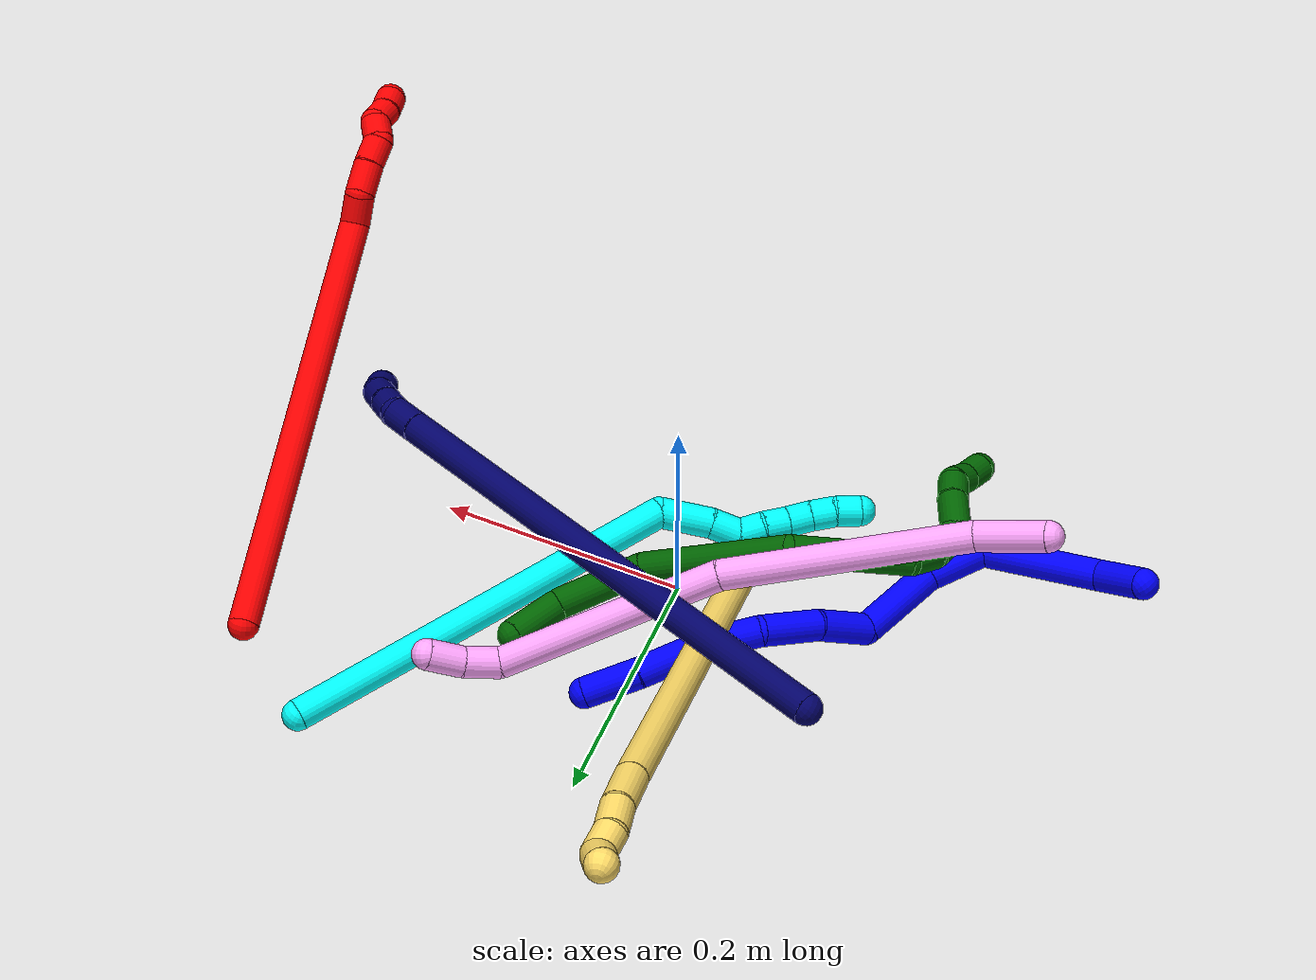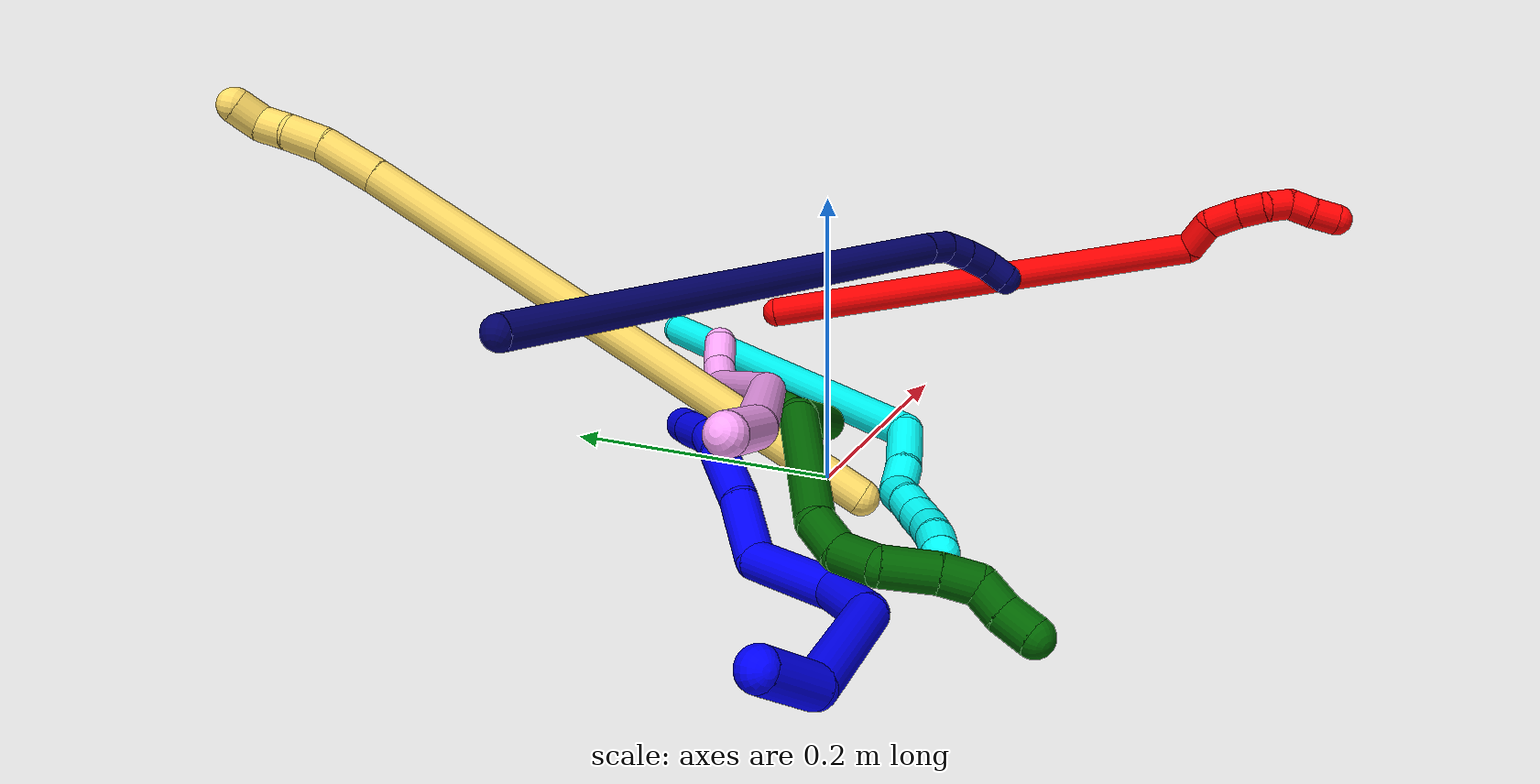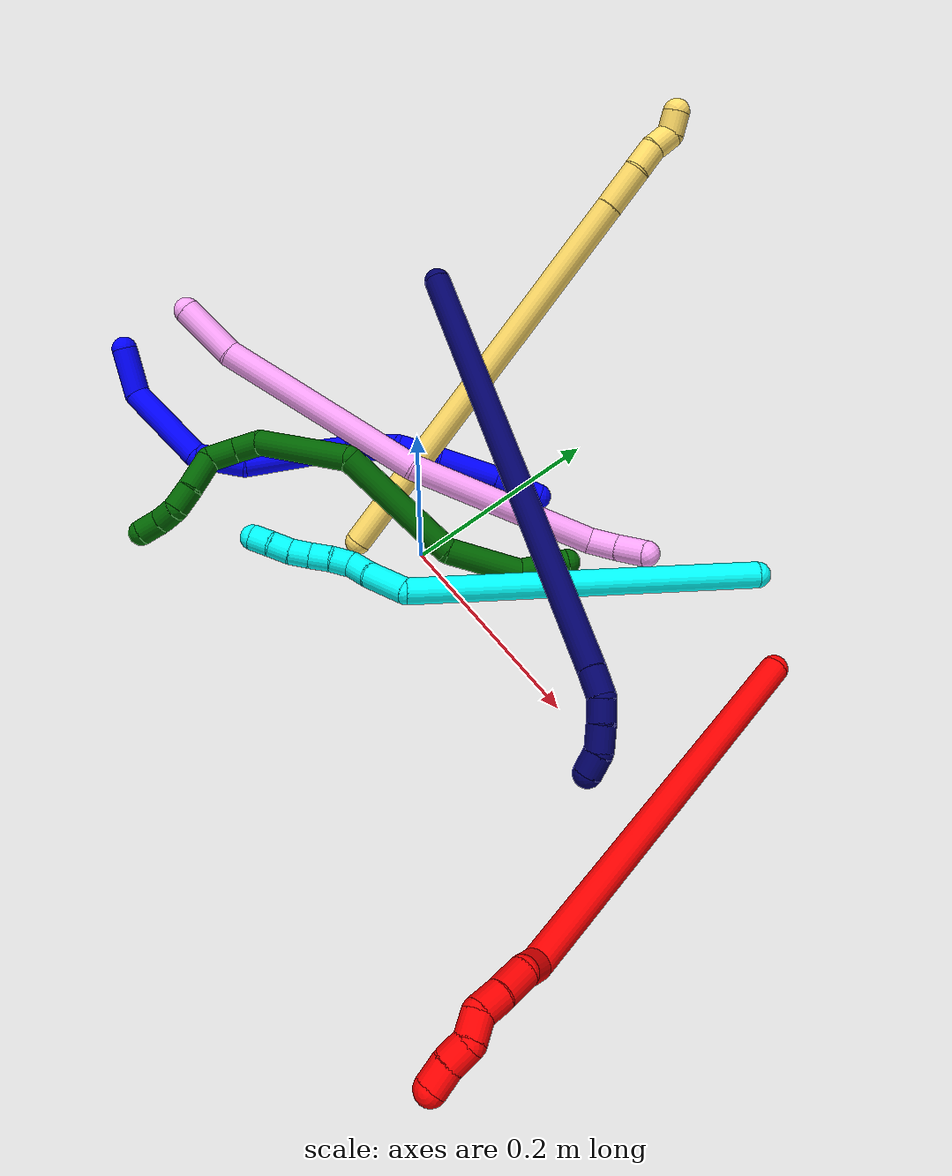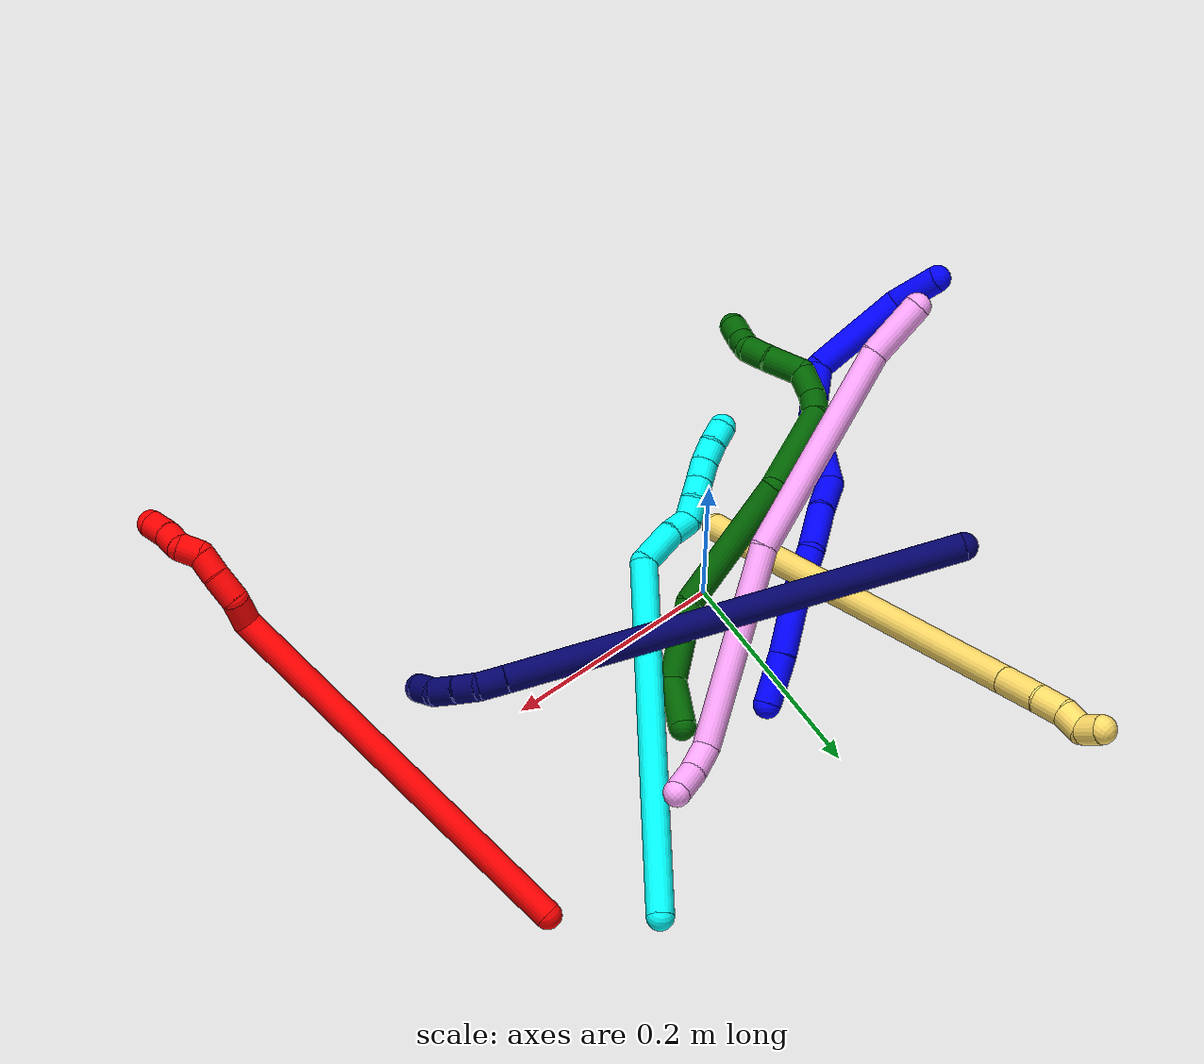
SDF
<sdf version="1.7">
 <world name="default">
  <plugin name="TubeGeneratorPlugin" filename="libtube_generator_plugin.so"/>
  <model name="photoneo_s_sensor">
   <static>1</static>
   <pose>0 0 2 1.57079 1.57079 3.14159</pose>
   <link name="link">
    <inertial><mass>0.1</mass></inertial>
    <sensor name="sensor" type="depth">
     <update_rate>30</update_rate>
     <camera>
      <horizontal_fov>1.22</horizontal_fov>
      <image><width>1920</width><height>1200</height><format>B8G8R8</format></image>
      <clip><near>0.1</near><far>4</far></clip>
      <depth_camera><output>points</output></depth_camera>
     </camera>
     <plugin name="camera_plugin" filename="libgazebo_ros_depth_camera.so">
      <baseline>0.2</baseline>
      <alwaysOn>1</alwaysOn>
      <updateRate>0.0</updateRate>
      <cameraName>camera_ir</cameraName>
      <imageTopicName>/camera/color/image_raw</imageTopicName>
      <cameraInfoTopicName>/camera/color/camera_info</cameraInfoTopicName>
      <depthImageTopicName>/camera/depth/image_raw</depthImageTopicName>
      <depthImageCameraInfoTopicName>/camera/depth/camera_info</depthImageCameraInfoTopicName>
      <pointCloudTopicName>/camera/depth/points</pointCloudTopicName>
      <frameName>fr_optical</frameName>
      <pointCloudCutoff>0.1</pointCloudCutoff>
      <pointCloudCutoffMax>2.0</pointCloudCutoffMax>
      <distortionK1>0</distortionK1>
      <distortionK2>0</distortionK2>
      <distortionK3>0</distortionK3>
      <distortionT1>0</distortionT1>
      <distortionT2>0</distortionT2>
      <CxPrime>0</CxPrime>
      <Cx>0</Cx>
      <Cy>0</Cy>
      <focalLength>0</focalLength>
      <hackBaseline>0</hackBaseline>
     </plugin>
    </sensor>
   </link>
  </model>
  <gravity>0 0 -9.8</gravity>
  <magnetic_field>6e-06 2.3e-05 -4.2e-05</magnetic_field>
  <atmosphere type="adiabatic"/>
  <physics name="default_physics" default="0" type="ode">
   <max_step_size>0.003</max_step_size>
   <real_time_factor>1</real_time_factor>
   <real_time_update_rate>1000</real_time_update_rate>
   <max_contacts>10000</max_contacts>
   <ode>
    <solver>
     <type>quick</type>
     <iters>100</iters>
     <sor>1.3</sor>
     <use_dynamic_moi_rescaling>0</use_dynamic_moi_rescaling>
    </solver>
    <constraints>
     <contact_max_correcting_vel>0</contact_max_correcting_vel>
     <contact_surface_layer>0.001</contact_surface_layer>
     <cfm>0</cfm>
     <erp>0.2</erp>
    </constraints>
   </ode>
  </physics>
  <scene><ambient>0.4 0.4 0.4 1</ambient><background>0.7 0.7 0.7 1</background><shadows>0</shadows></scene>
  <audio><device>default</device></audio>
  <spherical_coordinates>
   <surface_model>EARTH_WGS84</surface_model>
   <latitude_deg>0</latitude_deg>
   <longitude_deg>0</longitude_deg>
   <elevation>0</elevation>
   <heading_deg>0</heading_deg>
  </spherical_coordinates>
  <model name="bin">
   <static>1</static>
   <link name="bottom">
    <collision name="collision-bottom">
     <pose>0 0 -0.01 0 -0 0</pose>
     <geometry><box><size>0.8 0.6 0.02</size></box></geometry>
     <surface>
      <friction><ode><mu>100</mu><mu2>100</mu2></ode></friction>
      <contact><collide_bitmask>65535</collide_bitmask></contact>
     </surface>
    </collision>
   </link>
   <link name="west_wall">
    <collision name="collision-west_wall">
     <pose>-0.41 0 0.1 0 -0 0</pose>
     <geometry><box><size>0.02 0.6 0.2</size></box></geometry>
     <surface>
      <friction><ode><mu>100</mu><mu2>100</mu2></ode></friction>
      <contact><collide_bitmask>65535</collide_bitmask></contact>
     </surface>
    </collision>
   </link>
   <link name="east_wall">
    <collision name="collision-east_wall">
     <pose>0.41 0 0.1 0 -0 0</pose>
     <geometry><box><size>0.02 0.6 0.2</size></box></geometry>
     <surface>
      <friction><ode><mu>100</mu><mu2>100</mu2></ode></friction>
      <contact><collide_bitmask>65535</collide_bitmask></contact>
     </surface>
    </collision>
   </link>
   <link name="south_wall">
    <collision name="collision-south_wall">
     <pose>0 -0.31 0.1 0 -0 0</pose>
     <geometry><box><size>0.8 0.02 0.2</size></box></geometry>
     <surface>
      <friction><ode><mu>100</mu><mu2>100</mu2></ode></friction>
      <contact><collide_bitmask>65535</collide_bitmask></contact>
     </surface>
    </collision>
   </link>
   <link name="north_wall">
    <collision name="collision-north_wall">
     <pose>0 0.31 0.1 0 -0 0</pose>
     <geometry><box><size>0.8 0.02 0.2</size></box></geometry>
     <surface>
      <friction><ode><mu>100</mu><mu2>100</mu2></ode></friction>
      <contact><collide_bitmask>65535</collide_bitmask></contact>
     </surface>
    </collision>
   </link>
  </model>
  <model name="1">
   <static>0</static>
   <link name="1">
    <collision name="collision-cylinder-e_1_1_4">
     <pose>0.011284 -0.018383 -0.009575 2.05102 0.498534 0.794618</pose>
     <geometry><cylinder><radius>0.0125</radius><length>0.047199</length></cylinder></geometry>
     <surface>
      <friction><ode><mu>1.16</mu><mu2>1.16</mu2><slip1>0</slip1><slip2>0</slip2></ode></friction>
      <contact><ode><kp>1e+06</kp><kd>1</kd><max_vel>0</max_vel><min_depth>0.001</min_depth></ode></contact>
     </surface>
    </collision>
    <visual name="visual-cylinder-e_1_1_4">
     <pose>0.011284 -0.018383 -0.009575 2.05102 0.498534 0.794618</pose>
     <geometry><cylinder><radius>0.0125</radius><length>0.047199</length></cylinder></geometry>
     <material><ambient>0 0 1 1</ambient></material>
    </visual>
    <collision name="collision-cylinder-e_2_4_5">
     <pose>0.05737 -0.047546 -0.049607 2.80137 0.822556 2.39122</pose>
     <geometry><cylinder><radius>0.0125</radius><length>0.094974</length></cylinder></geometry>
     <surface>
      <friction><ode><mu>1.16</mu><mu2>1.16</mu2><slip1>0</slip1><slip2>0</slip2></ode></friction>
      <contact><ode><kp>1e+06</kp><kd>1</kd><max_vel>0</max_vel><min_depth>0.001</min_depth></ode></contact>
     </surface>
    </collision>
    <visual name="visual-cylinder-e_2_4_5">
     <pose>0.05737 -0.047546 -0.049607 2.80137 0.822556 2.39122</pose>
     <geometry><cylinder><radius>0.0125</radius><length>0.094974</length></cylinder></geometry>
     <material><ambient>0 0 1 1</ambient></material>
    </visual>
    <collision name="collision-cylinder-e_3_5_6">
     <pose>0.097305 -0.056148 -0.103307 -3.04811 0.216403 -2.32835</pose>
     <geometry><cylinder><radius>0.0125</radius><length>0.047808</length></cylinder></geometry>
     <surface>
      <friction><ode><mu>1.16</mu><mu2>1.16</mu2><slip1>0</slip1><slip2>0</slip2></ode></friction>
      <contact><ode><kp>1e+06</kp><kd>1</kd><max_vel>0</max_vel><min_depth>0.001</min_depth></ode></contact>
     </surface>
    </collision>
    <visual name="visual-cylinder-e_3_5_6">
     <pose>0.097305 -0.056148 -0.103307 -3.04811 0.216403 -2.32835</pose>
     <geometry><cylinder><radius>0.0125</radius><length>0.047808</length></cylinder></geometry>
     <material><ambient>0 0 1 1</ambient></material>
    </visual>
    <collision name="collision-cylinder-e_4_6_7">
     <pose>0.100575 -0.042153 -0.159298 -2.79532 -0.053452 0.303361</pose>
     <geometry><cylinder><radius>0.0125</radius><length>0.069725</length></cylinder></geometry>
     <surface>
      <friction><ode><mu>1.16</mu><mu2>1.16</mu2><slip1>0</slip1><slip2>0</slip2></ode></friction>
      <contact><ode><kp>1e+06</kp><kd>1</kd><max_vel>0</max_vel><min_depth>0.001</min_depth></ode></contact>
     </surface>
    </collision>
    <visual name="visual-cylinder-e_4_6_7">
     <pose>0.100575 -0.042153 -0.159298 -2.79532 -0.053452 0.303361</pose>
     <geometry><cylinder><radius>0.0125</radius><length>0.069725</length></cylinder></geometry>
     <material><ambient>0 0 1 1</ambient></material>
    </visual>
    <collision name="collision-cylinder-e_5_7_8">
     <pose>0.111567 -0.017863 -0.206488 -2.42923 0.592733 -1.37453</pose>
     <geometry><cylinder><radius>0.0125</radius><length>0.046021</length></cylinder></geometry>
     <surface>
      <friction><ode><mu>1.16</mu><mu2>1.16</mu2><slip1>0</slip1><slip2>0</slip2></ode></friction>
      <contact><ode><kp>1e+06</kp><kd>1</kd><max_vel>0</max_vel><min_depth>0.001</min_depth></ode></contact>
     </surface>
    </collision>
    <visual name="visual-cylinder-e_5_7_8">
     <pose>0.111567 -0.017863 -0.206488 -2.42923 0.592733 -1.37453</pose>
     <geometry><cylinder><radius>0.0125</radius><length>0.046021</length></cylinder></geometry>
     <material><ambient>0 0 1 1</ambient></material>
    </visual>
    <collision name="collision-cylinder-e_6_8_9">
     <pose>0.136008 0.004935 -0.24018 -2.64926 0.487725 -1.56101</pose>
     <geometry><cylinder><radius>0.0125</radius><length>0.049448</length></cylinder></geometry>
     <surface>
      <friction><ode><mu>1.16</mu><mu2>1.16</mu2><slip1>0</slip1><slip2>0</slip2></ode></friction>
      <contact><ode><kp>1e+06</kp><kd>1</kd><max_vel>0</max_vel><min_depth>0.001</min_depth></ode></contact>
     </surface>
    </collision>
    <visual name="visual-cylinder-e_6_8_9">
     <pose>0.136008 0.004935 -0.24018 -2.64926 0.487725 -1.56101</pose>
     <geometry><cylinder><radius>0.0125</radius><length>0.049448</length></cylinder></geometry>
     <material><ambient>0 0 1 1</ambient></material>
    </visual>
    <collision name="collision-cylinder-e_7_9_10">
     <pose>0.155527 0.016036 -0.278009 -3.09978 0.403207 -2.9377</pose>
     <geometry><cylinder><radius>0.0125</radius><length>0.04044</length></cylinder></geometry>
     <surface>
      <friction><ode><mu>1.16</mu><mu2>1.16</mu2><slip1>0</slip1><slip2>0</slip2></ode></friction>
      <contact><ode><kp>1e+06</kp><kd>1</kd><max_vel>0</max_vel><min_depth>0.001</min_depth></ode></contact>
     </surface>
    </collision>
    <visual name="visual-cylinder-e_7_9_10">
     <pose>0.155527 0.016036 -0.278009 -3.09978 0.403207 -2.9377</pose>
     <geometry><cylinder><radius>0.0125</radius><length>0.04044</length></cylinder></geometry>
     <material><ambient>0 0 1 1</ambient></material>
    </visual>
    <collision name="collision-cylinder-e_8_10_11">
     <pose>0.170339 0.015429 -0.324913 3.09272 0.237961 2.73825</pose>
     <geometry><cylinder><radius>0.0125</radius><length>0.058357</length></cylinder></geometry>
     <surface>
      <friction><ode><mu>1.16</mu><mu2>1.16</mu2><slip1>0</slip1><slip2>0</slip2></ode></friction>
      <contact><ode><kp>1e+06</kp><kd>1</kd><max_vel>0</max_vel><min_depth>0.001</min_depth></ode></contact>
     </surface>
    </collision>
    <visual name="visual-cylinder-e_8_10_11">
     <pose>0.170339 0.015429 -0.324913 3.09272 0.237961 2.73825</pose>
     <geometry><cylinder><radius>0.0125</radius><length>0.058357</length></cylinder></geometry>
     <material><ambient>0 0 1 1</ambient></material>
    </visual>
    <collision name="collision-cylinder-e_9_11_2">
     <pose>0.183823 0.011527 -0.375138 3.0272 0.291134 2.39691</pose>
     <geometry><cylinder><radius>0.0125</radius><length>0.046028</length></cylinder></geometry>
     <surface>
      <friction><ode><mu>1.16</mu><mu2>1.16</mu2><slip1>0</slip1><slip2>0</slip2></ode></friction>
      <contact><ode><kp>1e+06</kp><kd>1</kd><max_vel>0</max_vel><min_depth>0.001</min_depth></ode></contact>
     </surface>
    </collision>
    <visual name="visual-cylinder-e_9_11_2">
     <pose>0.183823 0.011527 -0.375138 3.0272 0.291134 2.39691</pose>
     <geometry><cylinder><radius>0.0125</radius><length>0.046028</length></cylinder></geometry>
     <material><ambient>0 0 1 1</ambient></material>
    </visual>
    <collision name="collision-sphere-2">
     <pose>0.190429 0.009011 -0.397039 0 -0 0</pose>
     <geometry><sphere><radius>0.0125</radius></sphere></geometry>
     <surface>
      <friction><ode><mu>1.16</mu><mu2>1.16</mu2><slip1>0</slip1><slip2>0</slip2></ode></friction>
      <contact><ode><kp>1e+06</kp><kd>1</kd><max_vel>0</max_vel><min_depth>0.001</min_depth></ode></contact>
     </surface>
    </collision>
    <visual name="visual-sphere-2">
     <pose>0.190429 0.009011 -0.397039 0 -0 0</pose>
     <geometry><sphere><radius>0.0125</radius></sphere></geometry>
     <material><ambient>0 0 1 1</ambient></material>
    </visual>
    <collision name="collision-sphere-11">
     <pose>0.177217 0.014043 -0.353236 0 -0 0</pose>
     <geometry><sphere><radius>0.0125</radius></sphere></geometry>
     <surface>
      <friction><ode><mu>1.16</mu><mu2>1.16</mu2><slip1>0</slip1><slip2>0</slip2></ode></friction>
      <contact><ode><kp>1e+06</kp><kd>1</kd><max_vel>0</max_vel><min_depth>0.001</min_depth></ode></contact>
     </surface>
    </collision>
    <visual name="visual-sphere-11">
     <pose>0.177217 0.014043 -0.353236 0 -0 0</pose>
     <geometry><sphere><radius>0.0125</radius></sphere></geometry>
     <material><ambient>0 0 1 1</ambient></material>
    </visual>
    <collision name="collision-sphere-10">
     <pose>0.163461 0.016814 -0.296591 0 -0 0</pose>
     <geometry><sphere><radius>0.0125</radius></sphere></geometry>
     <surface>
      <friction><ode><mu>1.16</mu><mu2>1.16</mu2><slip1>0</slip1><slip2>0</slip2></ode></friction>
      <contact><ode><kp>1e+06</kp><kd>1</kd><max_vel>0</max_vel><min_depth>0.001</min_depth></ode></contact>
     </surface>
    </collision>
    <visual name="visual-sphere-10">
     <pose>0.163461 0.016814 -0.296591 0 -0 0</pose>
     <geometry><sphere><radius>0.0125</radius></sphere></geometry>
     <material><ambient>0 0 1 1</ambient></material>
    </visual>
    <collision name="collision-sphere-9">
     <pose>0.147594 0.015259 -0.259427 0 -0 0</pose>
     <geometry><sphere><radius>0.0125</radius></sphere></geometry>
     <surface>
      <friction><ode><mu>1.16</mu><mu2>1.16</mu2><slip1>0</slip1><slip2>0</slip2></ode></friction>
      <contact><ode><kp>1e+06</kp><kd>1</kd><max_vel>0</max_vel><min_depth>0.001</min_depth></ode></contact>
     </surface>
    </collision>
    <visual name="visual-sphere-9">
     <pose>0.147594 0.015259 -0.259427 0 -0 0</pose>
     <geometry><sphere><radius>0.0125</radius></sphere></geometry>
     <material><ambient>0 0 1 1</ambient></material>
    </visual>
    <collision name="collision-sphere-4">
     <pose>0.022568 -0.036765 -0.019151 0 -0 0</pose>
     <geometry><sphere><radius>0.0125</radius></sphere></geometry>
     <surface>
      <friction><ode><mu>1.16</mu><mu2>1.16</mu2><slip1>0</slip1><slip2>0</slip2></ode></friction>
      <contact><ode><kp>1e+06</kp><kd>1</kd><max_vel>0</max_vel><min_depth>0.001</min_depth></ode></contact>
     </surface>
    </collision>
    <visual name="visual-sphere-4">
     <pose>0.022568 -0.036765 -0.019151 0 -0 0</pose>
     <geometry><sphere><radius>0.0125</radius></sphere></geometry>
     <material><ambient>0 0 1 1</ambient></material>
    </visual>
    <collision name="collision-sphere-1">
     <geometry><sphere><radius>0.0125</radius></sphere></geometry>
     <surface>
      <friction><ode><mu>1.16</mu><mu2>1.16</mu2><slip1>0</slip1><slip2>0</slip2></ode></friction>
      <contact><ode><kp>1e+06</kp><kd>1</kd><max_vel>0</max_vel><min_depth>0.001</min_depth></ode></contact>
     </surface>
    </collision>
    <visual name="visual-sphere-1">
     <geometry><sphere><radius>0.0125</radius></sphere></geometry>
     <material><ambient>0 0 1 1</ambient></material>
    </visual>
    <collision name="collision-sphere-8">
     <pose>0.124422 -0.005389 -0.220933 0 -0 0</pose>
     <geometry><sphere><radius>0.0125</radius></sphere></geometry>
     <surface>
      <friction><ode><mu>1.16</mu><mu2>1.16</mu2><slip1>0</slip1><slip2>0</slip2></ode></friction>
      <contact><ode><kp>1e+06</kp><kd>1</kd><max_vel>0</max_vel><min_depth>0.001</min_depth></ode></contact>
     </surface>
    </collision>
    <visual name="visual-sphere-8">
     <pose>0.124422 -0.005389 -0.220933 0 -0 0</pose>
     <geometry><sphere><radius>0.0125</radius></sphere></geometry>
     <material><ambient>0 0 1 1</ambient></material>
    </visual>
    <collision name="collision-sphere-5">
     <pose>0.092173 -0.058327 -0.080062 0 -0 0</pose>
     <geometry><sphere><radius>0.0125</radius></sphere></geometry>
     <surface>
      <friction><ode><mu>1.16</mu><mu2>1.16</mu2><slip1>0</slip1><slip2>0</slip2></ode></friction>
      <contact><ode><kp>1e+06</kp><kd>1</kd><max_vel>0</max_vel><min_depth>0.001</min_depth></ode></contact>
     </surface>
    </collision>
    <visual name="visual-sphere-5">
     <pose>0.092173 -0.058327 -0.080062 0 -0 0</pose>
     <geometry><sphere><radius>0.0125</radius></sphere></geometry>
     <material><ambient>0 0 1 1</ambient></material>
    </visual>
    <collision name="collision-sphere-6">
     <pose>0.102438 -0.053969 -0.126551 0 -0 0</pose>
     <geometry><sphere><radius>0.0125</radius></sphere></geometry>
     <surface>
      <friction><ode><mu>1.16</mu><mu2>1.16</mu2><slip1>0</slip1><slip2>0</slip2></ode></friction>
      <contact><ode><kp>1e+06</kp><kd>1</kd><max_vel>0</max_vel><min_depth>0.001</min_depth></ode></contact>
     </surface>
    </collision>
    <visual name="visual-sphere-6">
     <pose>0.102438 -0.053969 -0.126551 0 -0 0</pose>
     <geometry><sphere><radius>0.0125</radius></sphere></geometry>
     <material><ambient>0 0 1 1</ambient></material>
    </visual>
    <collision name="collision-sphere-7">
     <pose>0.098713 -0.030338 -0.192044 0 -0 0</pose>
     <geometry><sphere><radius>0.0125</radius></sphere></geometry>
     <surface>
      <friction><ode><mu>1.16</mu><mu2>1.16</mu2><slip1>0</slip1><slip2>0</slip2></ode></friction>
      <contact><ode><kp>1e+06</kp><kd>1</kd><max_vel>0</max_vel><min_depth>0.001</min_depth></ode></contact>
     </surface>
    </collision>
    <visual name="visual-sphere-7">
     <pose>0.098713 -0.030338 -0.192044 0 -0 0</pose>
     <geometry><sphere><radius>0.0125</radius></sphere></geometry>
     <material><ambient>0 0 1 1</ambient></material>
    </visual>
    <inertial>
     <pose>0.108393 -0.019011 -0.180118 0 -0 0</pose>
     <mass>0.5</mass>
     <inertia>
      <ixx>1.4e-05</ixx>
      <ixy>0</ixy>
      <ixz>0</ixz>
      <iyy>0.000118</iyy>
      <iyz>0</iyz>
      <izz>-0.000108</izz>
     </inertia>
    </inertial>
   </link>
   <pose>-0.345218 -0.109674 0.060497 1.16259 -0.463222 -0.430431</pose>
  </model>
  <model name="2">
   <static>0</static>
   <link name="2">
    <collision name="collision-cylinder-e_1_1_4">
     <pose>0.073476 -0.110008 0.12536 0.720267 0.414965 0.158208</pose>
     <geometry><cylinder><radius>0.0125</radius><length>0.364503</length></cylinder></geometry>
     <surface>
      <friction><ode><mu>1.16</mu><mu2>1.16</mu2><slip1>0</slip1><slip2>0</slip2></ode></friction>
      <contact><ode><kp>1e+06</kp><kd>1</kd><max_vel>0</max_vel><min_depth>0.001</min_depth></ode></contact>
     </surface>
    </collision>
    <visual name="visual-cylinder-e_1_1_4">
     <pose>0.073476 -0.110008 0.12536 0.720267 0.414965 0.158208</pose>
     <geometry><cylinder><radius>0.0125</radius><length>0.364503</length></cylinder></geometry>
     <material><ambient>1 0 0 1</ambient></material>
    </visual>
    <collision name="collision-cylinder-e_2_4_5">
     <pose>0.147251 -0.220273 0.263848 0.019518 0.022736 0.000222</pose>
     <geometry><cylinder><radius>0.0125</radius><length>0.026268</length></cylinder></geometry>
     <surface>
      <friction><ode><mu>1.16</mu><mu2>1.16</mu2><slip1>0</slip1><slip2>0</slip2></ode></friction>
      <contact><ode><kp>1e+06</kp><kd>1</kd><max_vel>0</max_vel><min_depth>0.001</min_depth></ode></contact>
     </surface>
    </collision>
    <visual name="visual-cylinder-e_2_4_5">
     <pose>0.147251 -0.220273 0.263848 0.019518 0.022736 0.000222</pose>
     <geometry><cylinder><radius>0.0125</radius><length>0.026268</length></cylinder></geometry>
     <material><ambient>1 0 0 1</ambient></material>
    </visual>
    <collision name="collision-cylinder-e_3_5_6">
     <pose>0.151189 -0.227043 0.288011 0.533239 0.276725 0.076029</pose>
     <geometry><cylinder><radius>0.0125</radius><length>0.026641</length></cylinder></geometry>
     <surface>
      <friction><ode><mu>1.16</mu><mu2>1.16</mu2><slip1>0</slip1><slip2>0</slip2></ode></friction>
      <contact><ode><kp>1e+06</kp><kd>1</kd><max_vel>0</max_vel><min_depth>0.001</min_depth></ode></contact>
     </surface>
    </collision>
    <visual name="visual-cylinder-e_3_5_6">
     <pose>0.151189 -0.227043 0.288011 0.533239 0.276725 0.076029</pose>
     <geometry><cylinder><radius>0.0125</radius><length>0.026641</length></cylinder></geometry>
     <material><ambient>1 0 0 1</ambient></material>
    </visual>
    <collision name="collision-cylinder-e_4_6_7">
     <pose>0.157369 -0.240131 0.307593 0.655674 0.231397 0.079012</pose>
     <geometry><cylinder><radius>0.0125</radius><length>0.022159</length></cylinder></geometry>
     <surface>
      <friction><ode><mu>1.16</mu><mu2>1.16</mu2><slip1>0</slip1><slip2>0</slip2></ode></friction>
      <contact><ode><kp>1e+06</kp><kd>1</kd><max_vel>0</max_vel><min_depth>0.001</min_depth></ode></contact>
     </surface>
    </collision>
    <visual name="visual-cylinder-e_4_6_7">
     <pose>0.157369 -0.240131 0.307593 0.655674 0.231397 0.079012</pose>
     <geometry><cylinder><radius>0.0125</radius><length>0.022159</length></cylinder></geometry>
     <material><ambient>1 0 0 1</ambient></material>
    </visual>
    <collision name="collision-cylinder-e_5_7_8">
     <pose>0.167388 -0.251357 0.321259 0.737608 0.824425 0.334831</pose>
     <geometry><cylinder><radius>0.0125</radius><length>0.020371</length></cylinder></geometry>
     <surface>
      <friction><ode><mu>1.16</mu><mu2>1.16</mu2><slip1>0</slip1><slip2>0</slip2></ode></friction>
      <contact><ode><kp>1e+06</kp><kd>1</kd><max_vel>0</max_vel><min_depth>0.001</min_depth></ode></contact>
     </surface>
    </collision>
    <visual name="visual-cylinder-e_5_7_8">
     <pose>0.167388 -0.251357 0.321259 0.737608 0.824425 0.334831</pose>
     <geometry><cylinder><radius>0.0125</radius><length>0.020371</length></cylinder></geometry>
     <material><ambient>1 0 0 1</ambient></material>
    </visual>
    <collision name="collision-cylinder-e_6_8_9">
     <pose>0.178291 -0.26506 0.328903 1.29875 0.349541 0.266524</pose>
     <geometry><cylinder><radius>0.0125</radius><length>0.020005</length></cylinder></geometry>
     <surface>
      <friction><ode><mu>1.16</mu><mu2>1.16</mu2><slip1>0</slip1><slip2>0</slip2></ode></friction>
      <contact><ode><kp>1e+06</kp><kd>1</kd><max_vel>0</max_vel><min_depth>0.001</min_depth></ode></contact>
     </surface>
    </collision>
    <visual name="visual-cylinder-e_6_8_9">
     <pose>0.178291 -0.26506 0.328903 1.29875 0.349541 0.266524</pose>
     <geometry><cylinder><radius>0.0125</radius><length>0.020005</length></cylinder></geometry>
     <material><ambient>1 0 0 1</ambient></material>
    </visual>
    <collision name="collision-cylinder-e_7_9_2">
     <pose>0.186893 -0.282211 0.334281 1.23216 0.542522 0.388841</pose>
     <geometry><cylinder><radius>0.0125</radius><length>0.020053</length></cylinder></geometry>
     <surface>
      <friction><ode><mu>1.16</mu><mu2>1.16</mu2><slip1>0</slip1><slip2>0</slip2></ode></friction>
      <contact><ode><kp>1e+06</kp><kd>1</kd><max_vel>0</max_vel><min_depth>0.001</min_depth></ode></contact>
     </surface>
    </collision>
    <visual name="visual-cylinder-e_7_9_2">
     <pose>0.186893 -0.282211 0.334281 1.23216 0.542522 0.388841</pose>
     <geometry><cylinder><radius>0.0125</radius><length>0.020053</length></cylinder></geometry>
     <material><ambient>1 0 0 1</ambient></material>
    </visual>
    <collision name="collision-sphere-2">
     <pose>0.19207 -0.29031 0.337133 0 -0 0</pose>
     <geometry><sphere><radius>0.0125</radius></sphere></geometry>
     <surface>
      <friction><ode><mu>1.16</mu><mu2>1.16</mu2><slip1>0</slip1><slip2>0</slip2></ode></friction>
      <contact><ode><kp>1e+06</kp><kd>1</kd><max_vel>0</max_vel><min_depth>0.001</min_depth></ode></contact>
     </surface>
    </collision>
    <visual name="visual-sphere-2">
     <pose>0.19207 -0.29031 0.337133 0 -0 0</pose>
     <geometry><sphere><radius>0.0125</radius></sphere></geometry>
     <material><ambient>1 0 0 1</ambient></material>
    </visual>
    <collision name="collision-sphere-9">
     <pose>0.181716 -0.274112 0.331428 0 -0 0</pose>
     <geometry><sphere><radius>0.0125</radius></sphere></geometry>
     <surface>
      <friction><ode><mu>1.16</mu><mu2>1.16</mu2><slip1>0</slip1><slip2>0</slip2></ode></friction>
      <contact><ode><kp>1e+06</kp><kd>1</kd><max_vel>0</max_vel><min_depth>0.001</min_depth></ode></contact>
     </surface>
    </collision>
    <visual name="visual-sphere-9">
     <pose>0.181716 -0.274112 0.331428 0 -0 0</pose>
     <geometry><sphere><radius>0.0125</radius></sphere></geometry>
     <material><ambient>1 0 0 1</ambient></material>
    </visual>
    <collision name="collision-sphere-4">
     <pose>0.146952 -0.220016 0.25072 0 -0 0</pose>
     <geometry><sphere><radius>0.0125</radius></sphere></geometry>
     <surface>
      <friction><ode><mu>1.16</mu><mu2>1.16</mu2><slip1>0</slip1><slip2>0</slip2></ode></friction>
      <contact><ode><kp>1e+06</kp><kd>1</kd><max_vel>0</max_vel><min_depth>0.001</min_depth></ode></contact>
     </surface>
    </collision>
    <visual name="visual-sphere-4">
     <pose>0.146952 -0.220016 0.25072 0 -0 0</pose>
     <geometry><sphere><radius>0.0125</radius></sphere></geometry>
     <material><ambient>1 0 0 1</ambient></material>
    </visual>
    <collision name="collision-sphere-1">
     <geometry><sphere><radius>0.0125</radius></sphere></geometry>
     <surface>
      <friction><ode><mu>1.16</mu><mu2>1.16</mu2><slip1>0</slip1><slip2>0</slip2></ode></friction>
      <contact><ode><kp>1e+06</kp><kd>1</kd><max_vel>0</max_vel><min_depth>0.001</min_depth></ode></contact>
     </surface>
    </collision>
    <visual name="visual-sphere-1">
     <geometry><sphere><radius>0.0125</radius></sphere></geometry>
     <material><ambient>1 0 0 1</ambient></material>
    </visual>
    <collision name="collision-sphere-8">
     <pose>0.174865 -0.256008 0.326378 0 -0 0</pose>
     <geometry><sphere><radius>0.0125</radius></sphere></geometry>
     <surface>
      <friction><ode><mu>1.16</mu><mu2>1.16</mu2><slip1>0</slip1><slip2>0</slip2></ode></friction>
      <contact><ode><kp>1e+06</kp><kd>1</kd><max_vel>0</max_vel><min_depth>0.001</min_depth></ode></contact>
     </surface>
    </collision>
    <visual name="visual-sphere-8">
     <pose>0.174865 -0.256008 0.326378 0 -0 0</pose>
     <geometry><sphere><radius>0.0125</radius></sphere></geometry>
     <material><ambient>1 0 0 1</ambient></material>
    </visual>
    <collision name="collision-sphere-5">
     <pose>0.147549 -0.220529 0.276976 0 -0 0</pose>
     <geometry><sphere><radius>0.0125</radius></sphere></geometry>
     <surface>
      <friction><ode><mu>1.16</mu><mu2>1.16</mu2><slip1>0</slip1><slip2>0</slip2></ode></friction>
      <contact><ode><kp>1e+06</kp><kd>1</kd><max_vel>0</max_vel><min_depth>0.001</min_depth></ode></contact>
     </surface>
    </collision>
    <visual name="visual-sphere-5">
     <pose>0.147549 -0.220529 0.276976 0 -0 0</pose>
     <geometry><sphere><radius>0.0125</radius></sphere></geometry>
     <material><ambient>1 0 0 1</ambient></material>
    </visual>
    <collision name="collision-sphere-6">
     <pose>0.154828 -0.233556 0.299045 0 -0 0</pose>
     <geometry><sphere><radius>0.0125</radius></sphere></geometry>
     <surface>
      <friction><ode><mu>1.16</mu><mu2>1.16</mu2><slip1>0</slip1><slip2>0</slip2></ode></friction>
      <contact><ode><kp>1e+06</kp><kd>1</kd><max_vel>0</max_vel><min_depth>0.001</min_depth></ode></contact>
     </surface>
    </collision>
    <visual name="visual-sphere-6">
     <pose>0.154828 -0.233556 0.299045 0 -0 0</pose>
     <geometry><sphere><radius>0.0125</radius></sphere></geometry>
     <material><ambient>1 0 0 1</ambient></material>
    </visual>
    <collision name="collision-sphere-7">
     <pose>0.15991 -0.246706 0.316141 0 -0 0</pose>
     <geometry><sphere><radius>0.0125</radius></sphere></geometry>
     <surface>
      <friction><ode><mu>1.16</mu><mu2>1.16</mu2><slip1>0</slip1><slip2>0</slip2></ode></friction>
      <contact><ode><kp>1e+06</kp><kd>1</kd><max_vel>0</max_vel><min_depth>0.001</min_depth></ode></contact>
     </surface>
    </collision>
    <visual name="visual-sphere-7">
     <pose>0.15991 -0.246706 0.316141 0 -0 0</pose>
     <geometry><sphere><radius>0.0125</radius></sphere></geometry>
     <material><ambient>1 0 0 1</ambient></material>
    </visual>
    <inertial>
     <pose>0.097779 -0.146672 0.173882 0 -0 0</pose>
     <mass>0.5</mass>
     <inertia>
      <ixx>0.004271</ixx>
      <ixy>0</ixy>
      <ixz>0</ixz>
      <iyy>0.003747</iyy>
      <iyz>0</iyz>
      <izz>0.00084</izz>
     </inertia>
    </inertial>
   </link>
   <pose>0.295709 0.174697 0.011499 0.525077 0.180394 -0.276996</pose>
  </model>
  <model name="3">
   <static>0</static>
   <link name="3">
    <collision name="collision-cylinder-e_1_1_4">
     <pose>-0.098345 -0.110403 -0.075612 2.17129 -0.633792 -1.11301</pose>
     <geometry><cylinder><radius>0.0125</radius><length>0.332131</length></cylinder></geometry>
     <surface>
      <friction><ode><mu>1.16</mu><mu2>1.16</mu2><slip1>0</slip1><slip2>0</slip2></ode></friction>
      <contact><ode><kp>1e+06</kp><kd>1</kd><max_vel>0</max_vel><min_depth>0.001</min_depth></ode></contact>
     </surface>
    </collision>
    <visual name="visual-cylinder-e_1_1_4">
     <pose>-0.098345 -0.110403 -0.075612 2.17129 -0.633792 -1.11301</pose>
     <geometry><cylinder><radius>0.0125</radius><length>0.332131</length></cylinder></geometry>
     <material><ambient>0.003922 1 0.996078 1</ambient></material>
    </visual>
    <collision name="collision-cylinder-e_2_4_5">
     <pose>-0.19767 -0.241809 -0.154843 1.74143 -0.045945 -0.054535</pose>
     <geometry><cylinder><radius>0.0125</radius><length>0.042669</length></cylinder></geometry>
     <surface>
      <friction><ode><mu>1.16</mu><mu2>1.16</mu2><slip1>0</slip1><slip2>0</slip2></ode></friction>
      <contact><ode><kp>1e+06</kp><kd>1</kd><max_vel>0</max_vel><min_depth>0.001</min_depth></ode></contact>
     </surface>
    </collision>
    <visual name="visual-cylinder-e_2_4_5">
     <pose>-0.19767 -0.241809 -0.154843 1.74143 -0.045945 -0.054535</pose>
     <geometry><cylinder><radius>0.0125</radius><length>0.042669</length></cylinder></geometry>
     <material><ambient>0.003922 1 0.996078 1</ambient></material>
    </visual>
    <collision name="collision-cylinder-e_3_5_6">
     <pose>-0.197643 -0.275086 -0.159163 1.62793 0.081686 0.086485</pose>
     <geometry><cylinder><radius>0.0125</radius><length>0.024671</length></cylinder></geometry>
     <surface>
      <friction><ode><mu>1.16</mu><mu2>1.16</mu2><slip1>0</slip1><slip2>0</slip2></ode></friction>
      <contact><ode><kp>1e+06</kp><kd>1</kd><max_vel>0</max_vel><min_depth>0.001</min_depth></ode></contact>
     </surface>
    </collision>
    <visual name="visual-cylinder-e_3_5_6">
     <pose>-0.197643 -0.275086 -0.159163 1.62793 0.081686 0.086485</pose>
     <geometry><cylinder><radius>0.0125</radius><length>0.024671</length></cylinder></geometry>
     <material><ambient>0.003922 1 0.996078 1</ambient></material>
    </visual>
    <collision name="collision-cylinder-e_4_6_7">
     <pose>-0.199799 -0.295397 -0.165316 2.16674 -0.314806 -0.581837</pose>
     <geometry><cylinder><radius>0.0125</radius><length>0.020426</length></cylinder></geometry>
     <surface>
      <friction><ode><mu>1.16</mu><mu2>1.16</mu2><slip1>0</slip1><slip2>0</slip2></ode></friction>
      <contact><ode><kp>1e+06</kp><kd>1</kd><max_vel>0</max_vel><min_depth>0.001</min_depth></ode></contact>
     </surface>
    </collision>
    <visual name="visual-cylinder-e_4_6_7">
     <pose>-0.199799 -0.295397 -0.165316 2.16674 -0.314806 -0.581837</pose>
     <geometry><cylinder><radius>0.0125</radius><length>0.020426</length></cylinder></geometry>
     <material><ambient>0.003922 1 0.996078 1</ambient></material>
    </visual>
    <collision name="collision-cylinder-e_5_7_8">
     <pose>-0.206585 -0.31198 -0.174547 1.9873 -0.369921 -0.559638</pose>
     <geometry><cylinder><radius>0.0125</radius><length>0.020046</length></cylinder></geometry>
     <surface>
      <friction><ode><mu>1.16</mu><mu2>1.16</mu2><slip1>0</slip1><slip2>0</slip2></ode></friction>
      <contact><ode><kp>1e+06</kp><kd>1</kd><max_vel>0</max_vel><min_depth>0.001</min_depth></ode></contact>
     </surface>
    </collision>
    <visual name="visual-cylinder-e_5_7_8">
     <pose>-0.206585 -0.31198 -0.174547 1.9873 -0.369921 -0.559638</pose>
     <geometry><cylinder><radius>0.0125</radius><length>0.020046</length></cylinder></geometry>
     <material><ambient>0.003922 1 0.996078 1</ambient></material>
    </visual>
    <collision name="collision-cylinder-e_6_8_9">
     <pose>-0.213742 -0.328763 -0.182777 2.06603 -0.36097 -0.593804</pose>
     <geometry><cylinder><radius>0.0125</radius><length>0.020012</length></cylinder></geometry>
     <surface>
      <friction><ode><mu>1.16</mu><mu2>1.16</mu2><slip1>0</slip1><slip2>0</slip2></ode></friction>
      <contact><ode><kp>1e+06</kp><kd>1</kd><max_vel>0</max_vel><min_depth>0.001</min_depth></ode></contact>
     </surface>
    </collision>
    <visual name="visual-cylinder-e_6_8_9">
     <pose>-0.213742 -0.328763 -0.182777 2.06603 -0.36097 -0.593804</pose>
     <geometry><cylinder><radius>0.0125</radius><length>0.020012</length></cylinder></geometry>
     <material><ambient>0.003922 1 0.996078 1</ambient></material>
    </visual>
    <collision name="collision-cylinder-e_7_9_10">
     <pose>-0.219232 -0.345315 -0.192442 2.13104 -0.196633 -0.352905</pose>
     <geometry><cylinder><radius>0.0125</radius><length>0.020017</length></cylinder></geometry>
     <surface>
      <friction><ode><mu>1.16</mu><mu2>1.16</mu2><slip1>0</slip1><slip2>0</slip2></ode></friction>
      <contact><ode><kp>1e+06</kp><kd>1</kd><max_vel>0</max_vel><min_depth>0.001</min_depth></ode></contact>
     </surface>
    </collision>
    <visual name="visual-cylinder-e_7_9_10">
     <pose>-0.219232 -0.345315 -0.192442 2.13104 -0.196633 -0.352905</pose>
     <geometry><cylinder><radius>0.0125</radius><length>0.020017</length></cylinder></geometry>
     <material><ambient>0.003922 1 0.996078 1</ambient></material>
    </visual>
    <collision name="collision-cylinder-e_8_10_2">
     <pose>-0.222865 -0.362826 -0.201248 1.94301 -0.168341 -0.245776</pose>
     <geometry><cylinder><radius>0.0125</radius><length>0.020028</length></cylinder></geometry>
     <surface>
      <friction><ode><mu>1.16</mu><mu2>1.16</mu2><slip1>0</slip1><slip2>0</slip2></ode></friction>
      <contact><ode><kp>1e+06</kp><kd>1</kd><max_vel>0</max_vel><min_depth>0.001</min_depth></ode></contact>
     </surface>
    </collision>
    <visual name="visual-cylinder-e_8_10_2">
     <pose>-0.222865 -0.362826 -0.201248 1.94301 -0.168341 -0.245776</pose>
     <geometry><cylinder><radius>0.0125</radius><length>0.020028</length></cylinder></geometry>
     <material><ambient>0.003922 1 0.996078 1</ambient></material>
    </visual>
    <collision name="collision-sphere-2">
     <pose>-0.224543 -0.372023 -0.204838 0 -0 0</pose>
     <geometry><sphere><radius>0.0125</radius></sphere></geometry>
     <surface>
      <friction><ode><mu>1.16</mu><mu2>1.16</mu2><slip1>0</slip1><slip2>0</slip2></ode></friction>
      <contact><ode><kp>1e+06</kp><kd>1</kd><max_vel>0</max_vel><min_depth>0.001</min_depth></ode></contact>
     </surface>
    </collision>
    <visual name="visual-sphere-2">
     <pose>-0.224543 -0.372023 -0.204838 0 -0 0</pose>
     <geometry><sphere><radius>0.0125</radius></sphere></geometry>
     <material><ambient>0.003922 1 0.996078 1</ambient></material>
    </visual>
    <collision name="collision-sphere-10">
     <pose>-0.221187 -0.35363 -0.197658 0 -0 0</pose>
     <geometry><sphere><radius>0.0125</radius></sphere></geometry>
     <surface>
      <friction><ode><mu>1.16</mu><mu2>1.16</mu2><slip1>0</slip1><slip2>0</slip2></ode></friction>
      <contact><ode><kp>1e+06</kp><kd>1</kd><max_vel>0</max_vel><min_depth>0.001</min_depth></ode></contact>
     </surface>
    </collision>
    <visual name="visual-sphere-10">
     <pose>-0.221187 -0.35363 -0.197658 0 -0 0</pose>
     <geometry><sphere><radius>0.0125</radius></sphere></geometry>
     <material><ambient>0.003922 1 0.996078 1</ambient></material>
    </visual>
    <collision name="collision-sphere-9">
     <pose>-0.217276 -0.337 -0.187226 0 -0 0</pose>
     <geometry><sphere><radius>0.0125</radius></sphere></geometry>
     <surface>
      <friction><ode><mu>1.16</mu><mu2>1.16</mu2><slip1>0</slip1><slip2>0</slip2></ode></friction>
      <contact><ode><kp>1e+06</kp><kd>1</kd><max_vel>0</max_vel><min_depth>0.001</min_depth></ode></contact>
     </surface>
    </collision>
    <visual name="visual-sphere-9">
     <pose>-0.217276 -0.337 -0.187226 0 -0 0</pose>
     <geometry><sphere><radius>0.0125</radius></sphere></geometry>
     <material><ambient>0.003922 1 0.996078 1</ambient></material>
    </visual>
    <collision name="collision-sphere-4">
     <pose>-0.19669 -0.220807 -0.151224 0 -0 0</pose>
     <geometry><sphere><radius>0.0125</radius></sphere></geometry>
     <surface>
      <friction><ode><mu>1.16</mu><mu2>1.16</mu2><slip1>0</slip1><slip2>0</slip2></ode></friction>
      <contact><ode><kp>1e+06</kp><kd>1</kd><max_vel>0</max_vel><min_depth>0.001</min_depth></ode></contact>
     </surface>
    </collision>
    <visual name="visual-sphere-4">
     <pose>-0.19669 -0.220807 -0.151224 0 -0 0</pose>
     <geometry><sphere><radius>0.0125</radius></sphere></geometry>
     <material><ambient>0.003922 1 0.996078 1</ambient></material>
    </visual>
    <collision name="collision-sphere-1">
     <geometry><sphere><radius>0.0125</radius></sphere></geometry>
     <surface>
      <friction><ode><mu>1.16</mu><mu2>1.16</mu2><slip1>0</slip1><slip2>0</slip2></ode></friction>
      <contact><ode><kp>1e+06</kp><kd>1</kd><max_vel>0</max_vel><min_depth>0.001</min_depth></ode></contact>
     </surface>
    </collision>
    <visual name="visual-sphere-1">
     <geometry><sphere><radius>0.0125</radius></sphere></geometry>
     <material><ambient>0.003922 1 0.996078 1</ambient></material>
    </visual>
    <collision name="collision-sphere-8">
     <pose>-0.210208 -0.320526 -0.178328 0 -0 0</pose>
     <geometry><sphere><radius>0.0125</radius></sphere></geometry>
     <surface>
      <friction><ode><mu>1.16</mu><mu2>1.16</mu2><slip1>0</slip1><slip2>0</slip2></ode></friction>
      <contact><ode><kp>1e+06</kp><kd>1</kd><max_vel>0</max_vel><min_depth>0.001</min_depth></ode></contact>
     </surface>
    </collision>
    <visual name="visual-sphere-8">
     <pose>-0.210208 -0.320526 -0.178328 0 -0 0</pose>
     <geometry><sphere><radius>0.0125</radius></sphere></geometry>
     <material><ambient>0.003922 1 0.996078 1</ambient></material>
    </visual>
    <collision name="collision-sphere-5">
     <pose>-0.19865 -0.262812 -0.158461 0 -0 0</pose>
     <geometry><sphere><radius>0.0125</radius></sphere></geometry>
     <surface>
      <friction><ode><mu>1.16</mu><mu2>1.16</mu2><slip1>0</slip1><slip2>0</slip2></ode></friction>
      <contact><ode><kp>1e+06</kp><kd>1</kd><max_vel>0</max_vel><min_depth>0.001</min_depth></ode></contact>
     </surface>
    </collision>
    <visual name="visual-sphere-5">
     <pose>-0.19865 -0.262812 -0.158461 0 -0 0</pose>
     <geometry><sphere><radius>0.0125</radius></sphere></geometry>
     <material><ambient>0.003922 1 0.996078 1</ambient></material>
    </visual>
    <collision name="collision-sphere-6">
     <pose>-0.196636 -0.28736 -0.159865 0 -0 0</pose>
     <geometry><sphere><radius>0.0125</radius></sphere></geometry>
     <surface>
      <friction><ode><mu>1.16</mu><mu2>1.16</mu2><slip1>0</slip1><slip2>0</slip2></ode></friction>
      <contact><ode><kp>1e+06</kp><kd>1</kd><max_vel>0</max_vel><min_depth>0.001</min_depth></ode></contact>
     </surface>
    </collision>
    <visual name="visual-sphere-6">
     <pose>-0.196636 -0.28736 -0.159865 0 -0 0</pose>
     <geometry><sphere><radius>0.0125</radius></sphere></geometry>
     <material><ambient>0.003922 1 0.996078 1</ambient></material>
    </visual>
    <collision name="collision-sphere-7">
     <pose>-0.202961 -0.303434 -0.170767 0 -0 0</pose>
     <geometry><sphere><radius>0.0125</radius></sphere></geometry>
     <surface>
      <friction><ode><mu>1.16</mu><mu2>1.16</mu2><slip1>0</slip1><slip2>0</slip2></ode></friction>
      <contact><ode><kp>1e+06</kp><kd>1</kd><max_vel>0</max_vel><min_depth>0.001</min_depth></ode></contact>
     </surface>
    </collision>
    <visual name="visual-sphere-7">
     <pose>-0.202961 -0.303434 -0.170767 0 -0 0</pose>
     <geometry><sphere><radius>0.0125</radius></sphere></geometry>
     <material><ambient>0.003922 1 0.996078 1</ambient></material>
    </visual>
    <inertial>
     <pose>-0.134651 -0.173637 -0.108126 0 -0 0</pose>
     <mass>0.5</mass>
     <inertia>
      <ixx>-0.001129</ixx>
      <ixy>0</ixy>
      <ixz>0</ixz>
      <iyy>-0.001674</iyy>
      <iyz>0</iyz>
      <izz>0.003857</izz>
     </inertia>
    </inertial>
   </link>
   <pose>0.218167 0.232363 0.011498 2.73946 -0.174403 1.89766</pose>
  </model>
  <model name="4">
   <static>0</static>
   <link name="4">
    <collision name="collision-cylinder-e_1_1_4">
     <pose>0.002273 0.007522 0.027255 -0.269299 0.080222 -0.010873</pose>
     <geometry><cylinder><radius>0.0125</radius><length>0.05673</length></cylinder></geometry>
     <surface>
      <friction><ode><mu>1.16</mu><mu2>1.16</mu2><slip1>0</slip1><slip2>0</slip2></ode></friction>
      <contact><ode><kp>1e+06</kp><kd>1</kd><max_vel>0</max_vel><min_depth>0.001</min_depth></ode></contact>
     </surface>
    </collision>
    <visual name="visual-cylinder-e_1_1_4">
     <pose>0.002273 0.007522 0.027255 -0.269299 0.080222 -0.010873</pose>
     <geometry><cylinder><radius>0.0125</radius><length>0.05673</length></cylinder></geometry>
     <material><ambient>1 0.65098 0.996078 1</ambient></material>
    </visual>
    <collision name="collision-cylinder-e_2_4_5">
     <pose>0.032391 0.051985 0.143174 -0.394763 0.282158 -0.05679</pose>
     <geometry><cylinder><radius>0.0125</radius><length>0.200013</length></cylinder></geometry>
     <surface>
      <friction><ode><mu>1.16</mu><mu2>1.16</mu2><slip1>0</slip1><slip2>0</slip2></ode></friction>
      <contact><ode><kp>1e+06</kp><kd>1</kd><max_vel>0</max_vel><min_depth>0.001</min_depth></ode></contact>
     </surface>
    </collision>
    <visual name="visual-cylinder-e_2_4_5">
     <pose>0.032391 0.051985 0.143174 -0.394763 0.282158 -0.05679</pose>
     <geometry><cylinder><radius>0.0125</radius><length>0.200013</length></cylinder></geometry>
     <material><ambient>1 0.65098 0.996078 1</ambient></material>
    </visual>
    <collision name="collision-cylinder-e_3_5_6">
     <pose>0.106191 0.119402 0.30586 -0.390562 0.521148 -0.105385</pose>
     <geometry><cylinder><radius>0.0125</radius><length>0.184606</length></cylinder></geometry>
     <surface>
      <friction><ode><mu>1.16</mu><mu2>1.16</mu2><slip1>0</slip1><slip2>0</slip2></ode></friction>
      <contact><ode><kp>1e+06</kp><kd>1</kd><max_vel>0</max_vel><min_depth>0.001</min_depth></ode></contact>
     </surface>
    </collision>
    <visual name="visual-cylinder-e_3_5_6">
     <pose>0.106191 0.119402 0.30586 -0.390562 0.521148 -0.105385</pose>
     <geometry><cylinder><radius>0.0125</radius><length>0.184606</length></cylinder></geometry>
     <material><ambient>1 0.65098 0.996078 1</ambient></material>
    </visual>
    <collision name="collision-cylinder-e_4_6_7">
     <pose>0.155295 0.160624 0.389163 -0.858465 0.218179 -0.100173</pose>
     <geometry><cylinder><radius>0.0125</radius><length>0.029089</length></cylinder></geometry>
     <surface>
      <friction><ode><mu>1.16</mu><mu2>1.16</mu2><slip1>0</slip1><slip2>0</slip2></ode></friction>
      <contact><ode><kp>1e+06</kp><kd>1</kd><max_vel>0</max_vel><min_depth>0.001</min_depth></ode></contact>
     </surface>
    </collision>
    <visual name="visual-cylinder-e_4_6_7">
     <pose>0.155295 0.160624 0.389163 -0.858465 0.218179 -0.100173</pose>
     <geometry><cylinder><radius>0.0125</radius><length>0.029089</length></cylinder></geometry>
     <material><ambient>1 0.65098 0.996078 1</ambient></material>
    </visual>
    <collision name="collision-cylinder-e_5_7_2">
     <pose>0.159261 0.183943 0.406174 -1.01951 0.055391 -0.030971</pose>
     <geometry><cylinder><radius>0.0125</radius><length>0.029561</length></cylinder></geometry>
     <surface>
      <friction><ode><mu>1.16</mu><mu2>1.16</mu2><slip1>0</slip1><slip2>0</slip2></ode></friction>
      <contact><ode><kp>1e+06</kp><kd>1</kd><max_vel>0</max_vel><min_depth>0.001</min_depth></ode></contact>
     </surface>
    </collision>
    <visual name="visual-cylinder-e_5_7_2">
     <pose>0.159261 0.183943 0.406174 -1.01951 0.055391 -0.030971</pose>
     <geometry><cylinder><radius>0.0125</radius><length>0.029561</length></cylinder></geometry>
     <material><ambient>1 0.65098 0.996078 1</ambient></material>
    </visual>
    <collision name="collision-sphere-2">
     <pose>0.16008 0.196514 0.413904 0 -0 0</pose>
     <geometry><sphere><radius>0.0125</radius></sphere></geometry>
     <surface>
      <friction><ode><mu>1.16</mu><mu2>1.16</mu2><slip1>0</slip1><slip2>0</slip2></ode></friction>
      <contact><ode><kp>1e+06</kp><kd>1</kd><max_vel>0</max_vel><min_depth>0.001</min_depth></ode></contact>
     </surface>
    </collision>
    <visual name="visual-sphere-2">
     <pose>0.16008 0.196514 0.413904 0 -0 0</pose>
     <geometry><sphere><radius>0.0125</radius></sphere></geometry>
     <material><ambient>1 0.65098 0.996078 1</ambient></material>
    </visual>
    <collision name="collision-sphere-7">
     <pose>0.158443 0.171371 0.398444 0 -0 0</pose>
     <geometry><sphere><radius>0.0125</radius></sphere></geometry>
     <surface>
      <friction><ode><mu>1.16</mu><mu2>1.16</mu2><slip1>0</slip1><slip2>0</slip2></ode></friction>
      <contact><ode><kp>1e+06</kp><kd>1</kd><max_vel>0</max_vel><min_depth>0.001</min_depth></ode></contact>
     </surface>
    </collision>
    <visual name="visual-sphere-7">
     <pose>0.158443 0.171371 0.398444 0 -0 0</pose>
     <geometry><sphere><radius>0.0125</radius></sphere></geometry>
     <material><ambient>1 0.65098 0.996078 1</ambient></material>
    </visual>
    <collision name="collision-sphere-6">
     <pose>0.152147 0.149877 0.379882 0 -0 0</pose>
     <geometry><sphere><radius>0.0125</radius></sphere></geometry>
     <surface>
      <friction><ode><mu>1.16</mu><mu2>1.16</mu2><slip1>0</slip1><slip2>0</slip2></ode></friction>
      <contact><ode><kp>1e+06</kp><kd>1</kd><max_vel>0</max_vel><min_depth>0.001</min_depth></ode></contact>
     </surface>
    </collision>
    <visual name="visual-sphere-6">
     <pose>0.152147 0.149877 0.379882 0 -0 0</pose>
     <geometry><sphere><radius>0.0125</radius></sphere></geometry>
     <material><ambient>1 0.65098 0.996078 1</ambient></material>
    </visual>
    <collision name="collision-sphere-5">
     <pose>0.060235 0.088926 0.231838 0 -0 0</pose>
     <geometry><sphere><radius>0.0125</radius></sphere></geometry>
     <surface>
      <friction><ode><mu>1.16</mu><mu2>1.16</mu2><slip1>0</slip1><slip2>0</slip2></ode></friction>
      <contact><ode><kp>1e+06</kp><kd>1</kd><max_vel>0</max_vel><min_depth>0.001</min_depth></ode></contact>
     </surface>
    </collision>
    <visual name="visual-sphere-5">
     <pose>0.060235 0.088926 0.231838 0 -0 0</pose>
     <geometry><sphere><radius>0.0125</radius></sphere></geometry>
     <material><ambient>1 0.65098 0.996078 1</ambient></material>
    </visual>
    <collision name="collision-sphere-1">
     <geometry><sphere><radius>0.0125</radius></sphere></geometry>
     <surface>
      <friction><ode><mu>1.16</mu><mu2>1.16</mu2><slip1>0</slip1><slip2>0</slip2></ode></friction>
      <contact><ode><kp>1e+06</kp><kd>1</kd><max_vel>0</max_vel><min_depth>0.001</min_depth></ode></contact>
     </surface>
    </collision>
    <visual name="visual-sphere-1">
     <geometry><sphere><radius>0.0125</radius></sphere></geometry>
     <material><ambient>1 0.65098 0.996078 1</ambient></material>
    </visual>
    <collision name="collision-sphere-4">
     <pose>0.004546 0.015045 0.05451 0 -0 0</pose>
     <geometry><sphere><radius>0.0125</radius></sphere></geometry>
     <surface>
      <friction><ode><mu>1.16</mu><mu2>1.16</mu2><slip1>0</slip1><slip2>0</slip2></ode></friction>
      <contact><ode><kp>1e+06</kp><kd>1</kd><max_vel>0</max_vel><min_depth>0.001</min_depth></ode></contact>
     </surface>
    </collision>
    <visual name="visual-sphere-4">
     <pose>0.004546 0.015045 0.05451 0 -0 0</pose>
     <geometry><sphere><radius>0.0125</radius></sphere></geometry>
     <material><ambient>1 0.65098 0.996078 1</ambient></material>
    </visual>
    <inertial>
     <pose>0.070873 0.085954 0.219948 0 -0 0</pose>
     <mass>0.5</mass>
     <inertia>
      <ixx>0.001056</ixx>
      <ixy>0</ixy>
      <ixz>0</ixz>
      <iyy>0.001075</iyy>
      <iyz>0</iyz>
      <izz>-0.000857</izz>
     </inertia>
    </inertial>
   </link>
   <pose>-0.275817 -0.060499 0.14744 2.14758 0.363947 1.77055</pose>
  </model>
  <model name="5">
   <static>0</static>
   <link name="5">
    <collision name="collision-cylinder-e_1_1_4">
     <pose>0.004282 0.073663 0.180706 -0.387077 0.021942 -0.004301</pose>
     <geometry><cylinder><radius>0.0125</radius><length>0.39038</length></cylinder></geometry>
     <surface>
      <friction><ode><mu>1.16</mu><mu2>1.16</mu2><slip1>0</slip1><slip2>0</slip2></ode></friction>
      <contact><ode><kp>1e+06</kp><kd>1</kd><max_vel>0</max_vel><min_depth>0.001</min_depth></ode></contact>
     </surface>
    </collision>
    <visual name="visual-cylinder-e_1_1_4">
     <pose>0.004282 0.073663 0.180706 -0.387077 0.021942 -0.004301</pose>
     <geometry><cylinder><radius>0.0125</radius><length>0.39038</length></cylinder></geometry>
     <material><ambient>1 0.858824 0.4 1</ambient></material>
    </visual>
    <collision name="collision-cylinder-e_2_4_5">
     <pose>0.009332 0.15436 0.380635 -0.350773 0.037482 -0.006643</pose>
     <geometry><cylinder><radius>0.0125</radius><length>0.040969</length></cylinder></geometry>
     <surface>
      <friction><ode><mu>1.16</mu><mu2>1.16</mu2><slip1>0</slip1><slip2>0</slip2></ode></friction>
      <contact><ode><kp>1e+06</kp><kd>1</kd><max_vel>0</max_vel><min_depth>0.001</min_depth></ode></contact>
     </surface>
    </collision>
    <visual name="visual-cylinder-e_2_4_5">
     <pose>0.009332 0.15436 0.380635 -0.350773 0.037482 -0.006643</pose>
     <geometry><cylinder><radius>0.0125</radius><length>0.040969</length></cylinder></geometry>
     <material><ambient>1 0.858824 0.4 1</ambient></material>
    </visual>
    <collision name="collision-cylinder-e_3_5_6">
     <pose>0.011359 0.163589 0.412695 -0.169308 0.096412 -0.008188</pose>
     <geometry><cylinder><radius>0.0125</radius><length>0.026166</length></cylinder></geometry>
     <surface>
      <friction><ode><mu>1.16</mu><mu2>1.16</mu2><slip1>0</slip1><slip2>0</slip2></ode></friction>
      <contact><ode><kp>1e+06</kp><kd>1</kd><max_vel>0</max_vel><min_depth>0.001</min_depth></ode></contact>
     </surface>
    </collision>
    <visual name="visual-cylinder-e_3_5_6">
     <pose>0.011359 0.163589 0.412695 -0.169308 0.096412 -0.008188</pose>
     <geometry><cylinder><radius>0.0125</radius><length>0.026166</length></cylinder></geometry>
     <material><ambient>1 0.858824 0.4 1</ambient></material>
    </visual>
    <collision name="collision-cylinder-e_4_6_7">
     <pose>0.011194 0.166421 0.43638 -0.058766 -0.130362 0.003837</pose>
     <geometry><cylinder><radius>0.0125</radius><length>0.021922</length></cylinder></geometry>
     <surface>
      <friction><ode><mu>1.16</mu><mu2>1.16</mu2><slip1>0</slip1><slip2>0</slip2></ode></friction>
      <contact><ode><kp>1e+06</kp><kd>1</kd><max_vel>0</max_vel><min_depth>0.001</min_depth></ode></contact>
     </surface>
    </collision>
    <visual name="visual-cylinder-e_4_6_7">
     <pose>0.011194 0.166421 0.43638 -0.058766 -0.130362 0.003837</pose>
     <geometry><cylinder><radius>0.0125</radius><length>0.021922</length></cylinder></geometry>
     <material><ambient>1 0.858824 0.4 1</ambient></material>
    </visual>
    <collision name="collision-cylinder-e_5_7_2">
     <pose>0.013603 0.172172 0.455284 -0.565559 0.382111 -0.112281</pose>
     <geometry><cylinder><radius>0.0125</radius><length>0.020563</length></cylinder></geometry>
     <surface>
      <friction><ode><mu>1.16</mu><mu2>1.16</mu2><slip1>0</slip1><slip2>0</slip2></ode></friction>
      <contact><ode><kp>1e+06</kp><kd>1</kd><max_vel>0</max_vel><min_depth>0.001</min_depth></ode></contact>
     </surface>
    </collision>
    <visual name="visual-cylinder-e_5_7_2">
     <pose>0.013603 0.172172 0.455284 -0.565559 0.382111 -0.112281</pose>
     <geometry><cylinder><radius>0.0125</radius><length>0.020563</length></cylinder></geometry>
     <material><ambient>1 0.858824 0.4 1</ambient></material>
    </visual>
    <collision name="collision-sphere-2">
     <pose>0.017437 0.177284 0.463338 0 -0 0</pose>
     <geometry><sphere><radius>0.0125</radius></sphere></geometry>
     <surface>
      <friction><ode><mu>1.16</mu><mu2>1.16</mu2><slip1>0</slip1><slip2>0</slip2></ode></friction>
      <contact><ode><kp>1e+06</kp><kd>1</kd><max_vel>0</max_vel><min_depth>0.001</min_depth></ode></contact>
     </surface>
    </collision>
    <visual name="visual-sphere-2">
     <pose>0.017437 0.177284 0.463338 0 -0 0</pose>
     <geometry><sphere><radius>0.0125</radius></sphere></geometry>
     <material><ambient>1 0.858824 0.4 1</ambient></material>
    </visual>
    <collision name="collision-sphere-7">
     <pose>0.009769 0.16706 0.447229 0 -0 0</pose>
     <geometry><sphere><radius>0.0125</radius></sphere></geometry>
     <surface>
      <friction><ode><mu>1.16</mu><mu2>1.16</mu2><slip1>0</slip1><slip2>0</slip2></ode></friction>
      <contact><ode><kp>1e+06</kp><kd>1</kd><max_vel>0</max_vel><min_depth>0.001</min_depth></ode></contact>
     </surface>
    </collision>
    <visual name="visual-sphere-7">
     <pose>0.009769 0.16706 0.447229 0 -0 0</pose>
     <geometry><sphere><radius>0.0125</radius></sphere></geometry>
     <material><ambient>1 0.858824 0.4 1</ambient></material>
    </visual>
    <collision name="collision-sphere-6">
     <pose>0.012619 0.165783 0.42553 0 -0 0</pose>
     <geometry><sphere><radius>0.0125</radius></sphere></geometry>
     <surface>
      <friction><ode><mu>1.16</mu><mu2>1.16</mu2><slip1>0</slip1><slip2>0</slip2></ode></friction>
      <contact><ode><kp>1e+06</kp><kd>1</kd><max_vel>0</max_vel><min_depth>0.001</min_depth></ode></contact>
     </surface>
    </collision>
    <visual name="visual-sphere-6">
     <pose>0.012619 0.165783 0.42553 0 -0 0</pose>
     <geometry><sphere><radius>0.0125</radius></sphere></geometry>
     <material><ambient>1 0.858824 0.4 1</ambient></material>
    </visual>
    <collision name="collision-sphere-5">
     <pose>0.0101 0.161395 0.399859 0 -0 0</pose>
     <geometry><sphere><radius>0.0125</radius></sphere></geometry>
     <surface>
      <friction><ode><mu>1.16</mu><mu2>1.16</mu2><slip1>0</slip1><slip2>0</slip2></ode></friction>
      <contact><ode><kp>1e+06</kp><kd>1</kd><max_vel>0</max_vel><min_depth>0.001</min_depth></ode></contact>
     </surface>
    </collision>
    <visual name="visual-sphere-5">
     <pose>0.0101 0.161395 0.399859 0 -0 0</pose>
     <geometry><sphere><radius>0.0125</radius></sphere></geometry>
     <material><ambient>1 0.858824 0.4 1</ambient></material>
    </visual>
    <collision name="collision-sphere-1">
     <geometry><sphere><radius>0.0125</radius></sphere></geometry>
     <surface>
      <friction><ode><mu>1.16</mu><mu2>1.16</mu2><slip1>0</slip1><slip2>0</slip2></ode></friction>
      <contact><ode><kp>1e+06</kp><kd>1</kd><max_vel>0</max_vel><min_depth>0.001</min_depth></ode></contact>
     </surface>
    </collision>
    <visual name="visual-sphere-1">
     <geometry><sphere><radius>0.0125</radius></sphere></geometry>
     <material><ambient>1 0.858824 0.4 1</ambient></material>
    </visual>
    <collision name="collision-sphere-4">
     <pose>0.008565 0.147326 0.361411 0 -0 0</pose>
     <geometry><sphere><radius>0.0125</radius></sphere></geometry>
     <surface>
      <friction><ode><mu>1.16</mu><mu2>1.16</mu2><slip1>0</slip1><slip2>0</slip2></ode></friction>
      <contact><ode><kp>1e+06</kp><kd>1</kd><max_vel>0</max_vel><min_depth>0.001</min_depth></ode></contact>
     </surface>
    </collision>
    <visual name="visual-sphere-4">
     <pose>0.008565 0.147326 0.361411 0 -0 0</pose>
     <geometry><sphere><radius>0.0125</radius></sphere></geometry>
     <material><ambient>1 0.858824 0.4 1</ambient></material>
    </visual>
    <inertial>
     <pose>0.005753 0.0931 0.23173 0 -0 0</pose>
     <mass>0.5</mass>
     <inertia>
      <ixx>0.004964</ixx>
      <ixy>0</ixy>
      <ixz>0</ixz>
      <iyy>0.00461</iyy>
      <iyz>0</iyz>
      <izz>-0.001954</izz>
     </inertia>
    </inertial>
   </link>
   <pose>-0.044284 -0.042279 0.011488 1.4283 -0.096743 -2.97596</pose>
  </model>
  <model name="6">
   <static>0</static>
   <link name="6">
    <collision name="collision-cylinder-e_1_1_4">
     <pose>-0.000566 0.003741 0.022543 -0.164467 -0.024784 0.002043</pose>
     <geometry><cylinder><radius>0.0125</radius><length>0.045716</length></cylinder></geometry>
     <surface>
      <friction><ode><mu>1.16</mu><mu2>1.16</mu2><slip1>0</slip1><slip2>0</slip2></ode></friction>
      <contact><ode><kp>1e+06</kp><kd>1</kd><max_vel>0</max_vel><min_depth>0.001</min_depth></ode></contact>
     </surface>
    </collision>
    <visual name="visual-cylinder-e_1_1_4">
     <pose>-0.000566 0.003741 0.022543 -0.164467 -0.024784 0.002043</pose>
     <geometry><cylinder><radius>0.0125</radius><length>0.045716</length></cylinder></geometry>
     <material><ambient>0 0.392157 0.003922 1</ambient></material>
    </visual>
    <collision name="collision-cylinder-e_2_4_5">
     <pose>-0.016485 0.003581 0.077812 0.118645 -0.435926 -0.026307</pose>
     <geometry><cylinder><radius>0.0125</radius><length>0.072718</length></cylinder></geometry>
     <surface>
      <friction><ode><mu>1.16</mu><mu2>1.16</mu2><slip1>0</slip1><slip2>0</slip2></ode></friction>
      <contact><ode><kp>1e+06</kp><kd>1</kd><max_vel>0</max_vel><min_depth>0.001</min_depth></ode></contact>
     </surface>
    </collision>
    <visual name="visual-cylinder-e_2_4_5">
     <pose>-0.016485 0.003581 0.077812 0.118645 -0.435926 -0.026307</pose>
     <geometry><cylinder><radius>0.0125</radius><length>0.072718</length></cylinder></geometry>
     <material><ambient>0 0.392157 0.003922 1</ambient></material>
    </visual>
    <collision name="collision-cylinder-e_3_5_6">
     <pose>-0.072323 -0.026922 0.150531 0.586981 -0.700354 -0.219868</pose>
     <geometry><cylinder><radius>0.0125</radius><length>0.125634</length></cylinder></geometry>
     <surface>
      <friction><ode><mu>1.16</mu><mu2>1.16</mu2><slip1>0</slip1><slip2>0</slip2></ode></friction>
      <contact><ode><kp>1e+06</kp><kd>1</kd><max_vel>0</max_vel><min_depth>0.001</min_depth></ode></contact>
     </surface>
    </collision>
    <visual name="visual-cylinder-e_3_5_6">
     <pose>-0.072323 -0.026922 0.150531 0.586981 -0.700354 -0.219868</pose>
     <geometry><cylinder><radius>0.0125</radius><length>0.125634</length></cylinder></geometry>
     <material><ambient>0 0.392157 0.003922 1</ambient></material>
    </visual>
    <collision name="collision-cylinder-e_4_6_7">
     <pose>-0.111375 -0.076664 0.234999 0.479732 0.028583 0.006991</pose>
     <geometry><cylinder><radius>0.0125</radius><length>0.100314</length></cylinder></geometry>
     <surface>
      <friction><ode><mu>1.16</mu><mu2>1.16</mu2><slip1>0</slip1><slip2>0</slip2></ode></friction>
      <contact><ode><kp>1e+06</kp><kd>1</kd><max_vel>0</max_vel><min_depth>0.001</min_depth></ode></contact>
     </surface>
    </collision>
    <visual name="visual-cylinder-e_4_6_7">
     <pose>-0.111375 -0.076664 0.234999 0.479732 0.028583 0.006991</pose>
     <geometry><cylinder><radius>0.0125</radius><length>0.100314</length></cylinder></geometry>
     <material><ambient>0 0.392157 0.003922 1</ambient></material>
    </visual>
    <collision name="collision-cylinder-e_5_7_8">
     <pose>-0.106643 -0.100675 0.292166 0.068507 0.253685 0.00874</pose>
     <geometry><cylinder><radius>0.0125</radius><length>0.026281</length></cylinder></geometry>
     <surface>
      <friction><ode><mu>1.16</mu><mu2>1.16</mu2><slip1>0</slip1><slip2>0</slip2></ode></friction>
      <contact><ode><kp>1e+06</kp><kd>1</kd><max_vel>0</max_vel><min_depth>0.001</min_depth></ode></contact>
     </surface>
    </collision>
    <visual name="visual-cylinder-e_5_7_8">
     <pose>-0.106643 -0.100675 0.292166 0.068507 0.253685 0.00874</pose>
     <geometry><cylinder><radius>0.0125</radius><length>0.026281</length></cylinder></geometry>
     <material><ambient>0 0.392157 0.003922 1</ambient></material>
    </visual>
    <collision name="collision-cylinder-e_6_8_9">
     <pose>-0.103244 -0.096932 0.317957 -0.338567 0.007287 -0.001245</pose>
     <geometry><cylinder><radius>0.0125</radius><length>0.027779</length></cylinder></geometry>
     <surface>
      <friction><ode><mu>1.16</mu><mu2>1.16</mu2><slip1>0</slip1><slip2>0</slip2></ode></friction>
      <contact><ode><kp>1e+06</kp><kd>1</kd><max_vel>0</max_vel><min_depth>0.001</min_depth></ode></contact>
     </surface>
    </collision>
    <visual name="visual-cylinder-e_6_8_9">
     <pose>-0.103244 -0.096932 0.317957 -0.338567 0.007287 -0.001245</pose>
     <geometry><cylinder><radius>0.0125</radius><length>0.027779</length></cylinder></geometry>
     <material><ambient>0 0.392157 0.003922 1</ambient></material>
    </visual>
    <collision name="collision-cylinder-e_7_9_10">
     <pose>-0.097002 -0.078976 0.340334 -0.963283 0.361294 -0.190353</pose>
     <geometry><cylinder><radius>0.0125</radius><length>0.034746</length></cylinder></geometry>
     <surface>
      <friction><ode><mu>1.16</mu><mu2>1.16</mu2><slip1>0</slip1><slip2>0</slip2></ode></friction>
      <contact><ode><kp>1e+06</kp><kd>1</kd><max_vel>0</max_vel><min_depth>0.001</min_depth></ode></contact>
     </surface>
    </collision>
    <visual name="visual-cylinder-e_7_9_10">
     <pose>-0.097002 -0.078976 0.340334 -0.963283 0.361294 -0.190353</pose>
     <geometry><cylinder><radius>0.0125</radius><length>0.034746</length></cylinder></geometry>
     <material><ambient>0 0.392157 0.003922 1</ambient></material>
    </visual>
    <collision name="collision-cylinder-e_8_10_11">
     <pose>-0.085725 -0.05783 0.357101 -0.80581 0.443356 -0.191538</pose>
     <geometry><cylinder><radius>0.0125</radius><length>0.023946</length></cylinder></geometry>
     <surface>
      <friction><ode><mu>1.16</mu><mu2>1.16</mu2><slip1>0</slip1><slip2>0</slip2></ode></friction>
      <contact><ode><kp>1e+06</kp><kd>1</kd><max_vel>0</max_vel><min_depth>0.001</min_depth></ode></contact>
     </surface>
    </collision>
    <visual name="visual-cylinder-e_8_10_11">
     <pose>-0.085725 -0.05783 0.357101 -0.80581 0.443356 -0.191538</pose>
     <geometry><cylinder><radius>0.0125</radius><length>0.023946</length></cylinder></geometry>
     <material><ambient>0 0.392157 0.003922 1</ambient></material>
    </visual>
    <collision name="collision-cylinder-e_9_11_12">
     <pose>-0.075017 -0.049372 0.373126 -0.076696 0.576929 -0.022769</pose>
     <geometry><cylinder><radius>0.0125</radius><length>0.020427</length></cylinder></geometry>
     <surface>
      <friction><ode><mu>1.16</mu><mu2>1.16</mu2><slip1>0</slip1><slip2>0</slip2></ode></friction>
      <contact><ode><kp>1e+06</kp><kd>1</kd><max_vel>0</max_vel><min_depth>0.001</min_depth></ode></contact>
     </surface>
    </collision>
    <visual name="visual-cylinder-e_9_11_12">
     <pose>-0.075017 -0.049372 0.373126 -0.076696 0.576929 -0.022769</pose>
     <geometry><cylinder><radius>0.0125</radius><length>0.020427</length></cylinder></geometry>
     <material><ambient>0 0.392157 0.003922 1</ambient></material>
    </visual>
    <collision name="collision-cylinder-e_10_12_2">
     <pose>-0.065591 -0.046541 0.391971 -0.207958 0.350746 -0.036978</pose>
     <geometry><cylinder><radius>0.0125</radius><length>0.022438</length></cylinder></geometry>
     <surface>
      <friction><ode><mu>1.16</mu><mu2>1.16</mu2><slip1>0</slip1><slip2>0</slip2></ode></friction>
      <contact><ode><kp>1e+06</kp><kd>1</kd><max_vel>0</max_vel><min_depth>0.001</min_depth></ode></contact>
     </surface>
    </collision>
    <visual name="visual-cylinder-e_10_12_2">
     <pose>-0.065591 -0.046541 0.391971 -0.207958 0.350746 -0.036978</pose>
     <geometry><cylinder><radius>0.0125</radius><length>0.022438</length></cylinder></geometry>
     <material><ambient>0 0.392157 0.003922 1</ambient></material>
    </visual>
    <collision name="collision-sphere-2">
     <pose>-0.061737 -0.044366 0.40228 0 -0 0</pose>
     <geometry><sphere><radius>0.0125</radius></sphere></geometry>
     <surface>
      <friction><ode><mu>1.16</mu><mu2>1.16</mu2><slip1>0</slip1><slip2>0</slip2></ode></friction>
      <contact><ode><kp>1e+06</kp><kd>1</kd><max_vel>0</max_vel><min_depth>0.001</min_depth></ode></contact>
     </surface>
    </collision>
    <visual name="visual-sphere-2">
     <pose>-0.061737 -0.044366 0.40228 0 -0 0</pose>
     <geometry><sphere><radius>0.0125</radius></sphere></geometry>
     <material><ambient>0 0.392157 0.003922 1</ambient></material>
    </visual>
    <collision name="collision-sphere-12">
     <pose>-0.069446 -0.048716 0.381662 0 -0 0</pose>
     <geometry><sphere><radius>0.0125</radius></sphere></geometry>
     <surface>
      <friction><ode><mu>1.16</mu><mu2>1.16</mu2><slip1>0</slip1><slip2>0</slip2></ode></friction>
      <contact><ode><kp>1e+06</kp><kd>1</kd><max_vel>0</max_vel><min_depth>0.001</min_depth></ode></contact>
     </surface>
    </collision>
    <visual name="visual-sphere-12">
     <pose>-0.069446 -0.048716 0.381662 0 -0 0</pose>
     <geometry><sphere><radius>0.0125</radius></sphere></geometry>
     <material><ambient>0 0.392157 0.003922 1</ambient></material>
    </visual>
    <collision name="collision-sphere-11">
     <pose>-0.080588 -0.050028 0.364591 0 -0 0</pose>
     <geometry><sphere><radius>0.0125</radius></sphere></geometry>
     <surface>
      <friction><ode><mu>1.16</mu><mu2>1.16</mu2><slip1>0</slip1><slip2>0</slip2></ode></friction>
      <contact><ode><kp>1e+06</kp><kd>1</kd><max_vel>0</max_vel><min_depth>0.001</min_depth></ode></contact>
     </surface>
    </collision>
    <visual name="visual-sphere-11">
     <pose>-0.080588 -0.050028 0.364591 0 -0 0</pose>
     <geometry><sphere><radius>0.0125</radius></sphere></geometry>
     <material><ambient>0 0.392157 0.003922 1</ambient></material>
    </visual>
    <collision name="collision-sphere-10">
     <pose>-0.090861 -0.065632 0.349611 0 -0 0</pose>
     <geometry><sphere><radius>0.0125</radius></sphere></geometry>
     <surface>
      <friction><ode><mu>1.16</mu><mu2>1.16</mu2><slip1>0</slip1><slip2>0</slip2></ode></friction>
      <contact><ode><kp>1e+06</kp><kd>1</kd><max_vel>0</max_vel><min_depth>0.001</min_depth></ode></contact>
     </surface>
    </collision>
    <visual name="visual-sphere-10">
     <pose>-0.090861 -0.065632 0.349611 0 -0 0</pose>
     <geometry><sphere><radius>0.0125</radius></sphere></geometry>
     <material><ambient>0 0.392157 0.003922 1</ambient></material>
    </visual>
    <collision name="collision-sphere-9">
     <pose>-0.103143 -0.092319 0.331058 0 -0 0</pose>
     <geometry><sphere><radius>0.0125</radius></sphere></geometry>
     <surface>
      <friction><ode><mu>1.16</mu><mu2>1.16</mu2><slip1>0</slip1><slip2>0</slip2></ode></friction>
      <contact><ode><kp>1e+06</kp><kd>1</kd><max_vel>0</max_vel><min_depth>0.001</min_depth></ode></contact>
     </surface>
    </collision>
    <visual name="visual-sphere-9">
     <pose>-0.103143 -0.092319 0.331058 0 -0 0</pose>
     <geometry><sphere><radius>0.0125</radius></sphere></geometry>
     <material><ambient>0 0.392157 0.003922 1</ambient></material>
    </visual>
    <collision name="collision-sphere-4">
     <pose>-0.001133 0.007483 0.045085 0 -0 0</pose>
     <geometry><sphere><radius>0.0125</radius></sphere></geometry>
     <surface>
      <friction><ode><mu>1.16</mu><mu2>1.16</mu2><slip1>0</slip1><slip2>0</slip2></ode></friction>
      <contact><ode><kp>1e+06</kp><kd>1</kd><max_vel>0</max_vel><min_depth>0.001</min_depth></ode></contact>
     </surface>
    </collision>
    <visual name="visual-sphere-4">
     <pose>-0.001133 0.007483 0.045085 0 -0 0</pose>
     <geometry><sphere><radius>0.0125</radius></sphere></geometry>
     <material><ambient>0 0.392157 0.003922 1</ambient></material>
    </visual>
    <collision name="collision-sphere-1">
     <geometry><sphere><radius>0.0125</radius></sphere></geometry>
     <surface>
      <friction><ode><mu>1.16</mu><mu2>1.16</mu2><slip1>0</slip1><slip2>0</slip2></ode></friction>
      <contact><ode><kp>1e+06</kp><kd>1</kd><max_vel>0</max_vel><min_depth>0.001</min_depth></ode></contact>
     </surface>
    </collision>
    <visual name="visual-sphere-1">
     <geometry><sphere><radius>0.0125</radius></sphere></geometry>
     <material><ambient>0 0.392157 0.003922 1</ambient></material>
    </visual>
    <collision name="collision-sphere-8">
     <pose>-0.103345 -0.101545 0.304857 0 -0 0</pose>
     <geometry><sphere><radius>0.0125</radius></sphere></geometry>
     <surface>
      <friction><ode><mu>1.16</mu><mu2>1.16</mu2><slip1>0</slip1><slip2>0</slip2></ode></friction>
      <contact><ode><kp>1e+06</kp><kd>1</kd><max_vel>0</max_vel><min_depth>0.001</min_depth></ode></contact>
     </surface>
    </collision>
    <visual name="visual-sphere-8">
     <pose>-0.103345 -0.101545 0.304857 0 -0 0</pose>
     <geometry><sphere><radius>0.0125</radius></sphere></geometry>
     <material><ambient>0 0.392157 0.003922 1</ambient></material>
    </visual>
    <collision name="collision-sphere-5">
     <pose>-0.031838 -0.00032 0.110539 0 -0 0</pose>
     <geometry><sphere><radius>0.0125</radius></sphere></geometry>
     <surface>
      <friction><ode><mu>1.16</mu><mu2>1.16</mu2><slip1>0</slip1><slip2>0</slip2></ode></friction>
      <contact><ode><kp>1e+06</kp><kd>1</kd><max_vel>0</max_vel><min_depth>0.001</min_depth></ode></contact>
     </surface>
    </collision>
    <visual name="visual-sphere-5">
     <pose>-0.031838 -0.00032 0.110539 0 -0 0</pose>
     <geometry><sphere><radius>0.0125</radius></sphere></geometry>
     <material><ambient>0 0.392157 0.003922 1</ambient></material>
    </visual>
    <collision name="collision-sphere-6">
     <pose>-0.112808 -0.053524 0.190522 0 -0 0</pose>
     <geometry><sphere><radius>0.0125</radius></sphere></geometry>
     <surface>
      <friction><ode><mu>1.16</mu><mu2>1.16</mu2><slip1>0</slip1><slip2>0</slip2></ode></friction>
      <contact><ode><kp>1e+06</kp><kd>1</kd><max_vel>0</max_vel><min_depth>0.001</min_depth></ode></contact>
     </surface>
    </collision>
    <visual name="visual-sphere-6">
     <pose>-0.112808 -0.053524 0.190522 0 -0 0</pose>
     <geometry><sphere><radius>0.0125</radius></sphere></geometry>
     <material><ambient>0 0.392157 0.003922 1</ambient></material>
    </visual>
    <collision name="collision-sphere-7">
     <pose>-0.109941 -0.099804 0.279476 0 -0 0</pose>
     <geometry><sphere><radius>0.0125</radius></sphere></geometry>
     <surface>
      <friction><ode><mu>1.16</mu><mu2>1.16</mu2><slip1>0</slip1><slip2>0</slip2></ode></friction>
      <contact><ode><kp>1e+06</kp><kd>1</kd><max_vel>0</max_vel><min_depth>0.001</min_depth></ode></contact>
     </surface>
    </collision>
    <visual name="visual-sphere-7">
     <pose>-0.109941 -0.099804 0.279476 0 -0 0</pose>
     <geometry><sphere><radius>0.0125</radius></sphere></geometry>
     <material><ambient>0 0.392157 0.003922 1</ambient></material>
    </visual>
    <inertial>
     <pose>-0.071163 -0.044323 0.204958 0 -0 0</pose>
     <mass>0.5</mass>
     <inertia>
      <ixx>0.000236</ixx>
      <ixy>0</ixy>
      <ixz>0</ixz>
      <iyy>0.000254</iyy>
      <iyz>0</iyz>
      <izz>0.000257</izz>
     </inertia>
    </inertial>
   </link>
   <pose>0.097308 0.099529 0.013044 1.90369 1.22227 -0.281968</pose>
  </model>
  <model name="7">
   <static>0</static>
   <link name="7">
    <collision name="collision-cylinder-e_1_1_4">
     <pose>0.152854 -0.04938 0.12818 0.367715 0.838727 0.165425</pose>
     <geometry><cylinder><radius>0.0125</radius><length>0.411013</length></cylinder></geometry>
     <surface>
      <friction><ode><mu>1.16</mu><mu2>1.16</mu2><slip1>0</slip1><slip2>0</slip2></ode></friction>
      <contact><ode><kp>1e+06</kp><kd>1</kd><max_vel>0</max_vel><min_depth>0.001</min_depth></ode></contact>
     </surface>
    </collision>
    <visual name="visual-cylinder-e_1_1_4">
     <pose>0.152854 -0.04938 0.12818 0.367715 0.838727 0.165425</pose>
     <geometry><cylinder><radius>0.0125</radius><length>0.411013</length></cylinder></geometry>
     <material><ambient>0.003922 0 0.403922 1</ambient></material>
    </visual>
    <collision name="collision-cylinder-e_2_4_5">
     <pose>0.315232 -0.101938 0.263609 0.413219 0.877364 0.196047</pose>
     <geometry><cylinder><radius>0.0125</radius><length>0.024767</length></cylinder></geometry>
     <surface>
      <friction><ode><mu>1.16</mu><mu2>1.16</mu2><slip1>0</slip1><slip2>0</slip2></ode></friction>
      <contact><ode><kp>1e+06</kp><kd>1</kd><max_vel>0</max_vel><min_depth>0.001</min_depth></ode></contact>
     </surface>
    </collision>
    <visual name="visual-cylinder-e_2_4_5">
     <pose>0.315232 -0.101938 0.263609 0.413219 0.877364 0.196047</pose>
     <geometry><cylinder><radius>0.0125</radius><length>0.024767</length></cylinder></geometry>
     <material><ambient>0.003922 0 0.403922 1</ambient></material>
    </visual>
    <collision name="collision-cylinder-e_3_5_6">
     <pose>0.333942 -0.109311 0.272972 1.10397 1.09814 0.720669</pose>
     <geometry><cylinder><radius>0.0125</radius><length>0.020635</length></cylinder></geometry>
     <surface>
      <friction><ode><mu>1.16</mu><mu2>1.16</mu2><slip1>0</slip1><slip2>0</slip2></ode></friction>
      <contact><ode><kp>1e+06</kp><kd>1</kd><max_vel>0</max_vel><min_depth>0.001</min_depth></ode></contact>
     </surface>
    </collision>
    <visual name="visual-cylinder-e_3_5_6">
     <pose>0.333942 -0.109311 0.272972 1.10397 1.09814 0.720669</pose>
     <geometry><cylinder><radius>0.0125</radius><length>0.020635</length></cylinder></geometry>
     <material><ambient>0.003922 0 0.403922 1</ambient></material>
    </visual>
    <collision name="collision-cylinder-e_4_6_7">
     <pose>0.353636 -0.11828 0.276219 1.33784 1.13386 0.932518</pose>
     <geometry><cylinder><radius>0.0125</radius><length>0.023196</length></cylinder></geometry>
     <surface>
      <friction><ode><mu>1.16</mu><mu2>1.16</mu2><slip1>0</slip1><slip2>0</slip2></ode></friction>
      <contact><ode><kp>1e+06</kp><kd>1</kd><max_vel>0</max_vel><min_depth>0.001</min_depth></ode></contact>
     </surface>
    </collision>
    <visual name="visual-cylinder-e_4_6_7">
     <pose>0.353636 -0.11828 0.276219 1.33784 1.13386 0.932518</pose>
     <geometry><cylinder><radius>0.0125</radius><length>0.023196</length></cylinder></geometry>
     <material><ambient>0.003922 0 0.403922 1</ambient></material>
    </visual>
    <collision name="collision-cylinder-e_5_7_2">
     <pose>0.372097 -0.128795 0.274569 2.02228 0.894782 1.30726</pose>
     <geometry><cylinder><radius>0.0125</radius><length>0.02039</length></cylinder></geometry>
     <surface>
      <friction><ode><mu>1.16</mu><mu2>1.16</mu2><slip1>0</slip1><slip2>0</slip2></ode></friction>
      <contact><ode><kp>1e+06</kp><kd>1</kd><max_vel>0</max_vel><min_depth>0.001</min_depth></ode></contact>
     </surface>
    </collision>
    <visual name="visual-cylinder-e_5_7_2">
     <pose>0.372097 -0.128795 0.274569 2.02228 0.894782 1.30726</pose>
     <geometry><cylinder><radius>0.0125</radius><length>0.02039</length></cylinder></geometry>
     <material><ambient>0.003922 0 0.403922 1</ambient></material>
    </visual>
    <collision name="collision-sphere-2">
     <pose>0.38005 -0.134535 0.271786 0 -0 0</pose>
     <geometry><sphere><radius>0.0125</radius></sphere></geometry>
     <surface>
      <friction><ode><mu>1.16</mu><mu2>1.16</mu2><slip1>0</slip1><slip2>0</slip2></ode></friction>
      <contact><ode><kp>1e+06</kp><kd>1</kd><max_vel>0</max_vel><min_depth>0.001</min_depth></ode></contact>
     </surface>
    </collision>
    <visual name="visual-sphere-2">
     <pose>0.38005 -0.134535 0.271786 0 -0 0</pose>
     <geometry><sphere><radius>0.0125</radius></sphere></geometry>
     <material><ambient>0.003922 0 0.403922 1</ambient></material>
    </visual>
    <collision name="collision-sphere-7">
     <pose>0.364144 -0.123056 0.277352 0 -0 0</pose>
     <geometry><sphere><radius>0.0125</radius></sphere></geometry>
     <surface>
      <friction><ode><mu>1.16</mu><mu2>1.16</mu2><slip1>0</slip1><slip2>0</slip2></ode></friction>
      <contact><ode><kp>1e+06</kp><kd>1</kd><max_vel>0</max_vel><min_depth>0.001</min_depth></ode></contact>
     </surface>
    </collision>
    <visual name="visual-sphere-7">
     <pose>0.364144 -0.123056 0.277352 0 -0 0</pose>
     <geometry><sphere><radius>0.0125</radius></sphere></geometry>
     <material><ambient>0.003922 0 0.403922 1</ambient></material>
    </visual>
    <collision name="collision-sphere-6">
     <pose>0.343128 -0.113505 0.275086 0 -0 0</pose>
     <geometry><sphere><radius>0.0125</radius></sphere></geometry>
     <surface>
      <friction><ode><mu>1.16</mu><mu2>1.16</mu2><slip1>0</slip1><slip2>0</slip2></ode></friction>
      <contact><ode><kp>1e+06</kp><kd>1</kd><max_vel>0</max_vel><min_depth>0.001</min_depth></ode></contact>
     </surface>
    </collision>
    <visual name="visual-sphere-6">
     <pose>0.343128 -0.113505 0.275086 0 -0 0</pose>
     <geometry><sphere><radius>0.0125</radius></sphere></geometry>
     <material><ambient>0.003922 0 0.403922 1</ambient></material>
    </visual>
    <collision name="collision-sphere-5">
     <pose>0.324756 -0.105116 0.270858 0 -0 0</pose>
     <geometry><sphere><radius>0.0125</radius></sphere></geometry>
     <surface>
      <friction><ode><mu>1.16</mu><mu2>1.16</mu2><slip1>0</slip1><slip2>0</slip2></ode></friction>
      <contact><ode><kp>1e+06</kp><kd>1</kd><max_vel>0</max_vel><min_depth>0.001</min_depth></ode></contact>
     </surface>
    </collision>
    <visual name="visual-sphere-5">
     <pose>0.324756 -0.105116 0.270858 0 -0 0</pose>
     <geometry><sphere><radius>0.0125</radius></sphere></geometry>
     <material><ambient>0.003922 0 0.403922 1</ambient></material>
    </visual>
    <collision name="collision-sphere-1">
     <geometry><sphere><radius>0.0125</radius></sphere></geometry>
     <surface>
      <friction><ode><mu>1.16</mu><mu2>1.16</mu2><slip1>0</slip1><slip2>0</slip2></ode></friction>
      <contact><ode><kp>1e+06</kp><kd>1</kd><max_vel>0</max_vel><min_depth>0.001</min_depth></ode></contact>
     </surface>
    </collision>
    <visual name="visual-sphere-1">
     <geometry><sphere><radius>0.0125</radius></sphere></geometry>
     <material><ambient>0.003922 0 0.403922 1</ambient></material>
    </visual>
    <collision name="collision-sphere-4">
     <pose>0.305708 -0.098759 0.25636 0 -0 0</pose>
     <geometry><sphere><radius>0.0125</radius></sphere></geometry>
     <surface>
      <friction><ode><mu>1.16</mu><mu2>1.16</mu2><slip1>0</slip1><slip2>0</slip2></ode></friction>
      <contact><ode><kp>1e+06</kp><kd>1</kd><max_vel>0</max_vel><min_depth>0.001</min_depth></ode></contact>
     </surface>
    </collision>
    <visual name="visual-sphere-4">
     <pose>0.305708 -0.098759 0.25636 0 -0 0</pose>
     <geometry><sphere><radius>0.0125</radius></sphere></geometry>
     <material><ambient>0.003922 0 0.403922 1</ambient></material>
    </visual>
    <inertial>
     <pose>0.186626 -0.060891 0.153701 0 -0 0</pose>
     <mass>0.5</mass>
     <inertia>
      <ixx>0.004499</ixx>
      <ixy>0</ixy>
      <ixz>0</ixz>
      <iyy>0.006232</iyy>
      <iyz>0</iyz>
      <izz>-0.002903</izz>
     </inertia>
    </inertial>
   </link>
   <pose>-0.164933 0.149392 0.139742 -0.384542 0.810419 -0.361364</pose>
  </model>
 </world>
</sdf>
